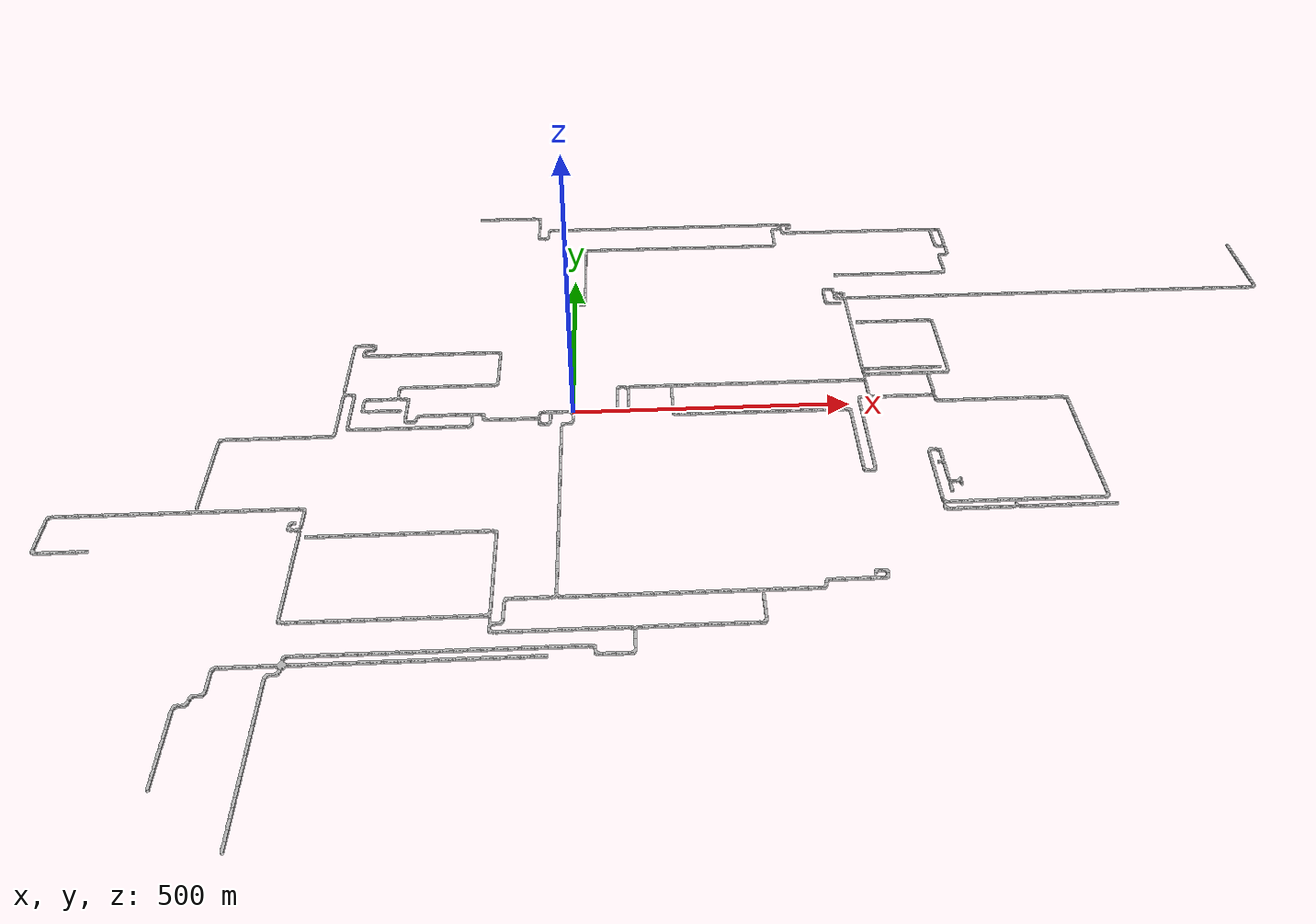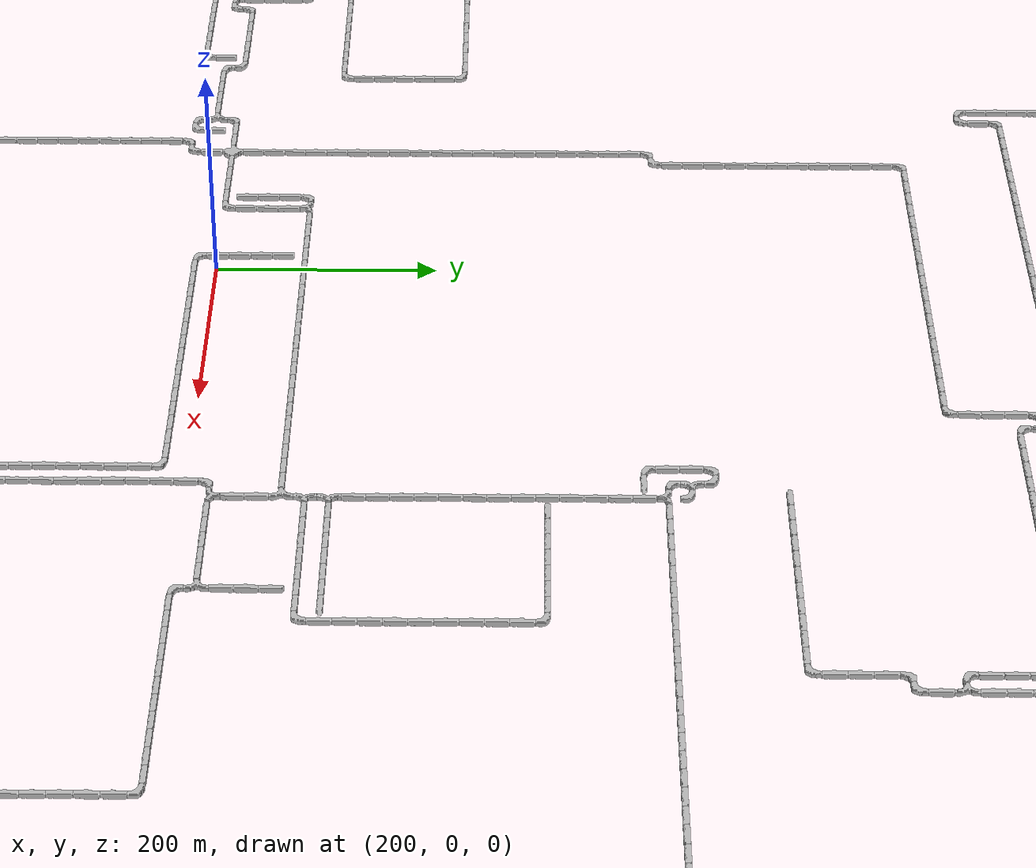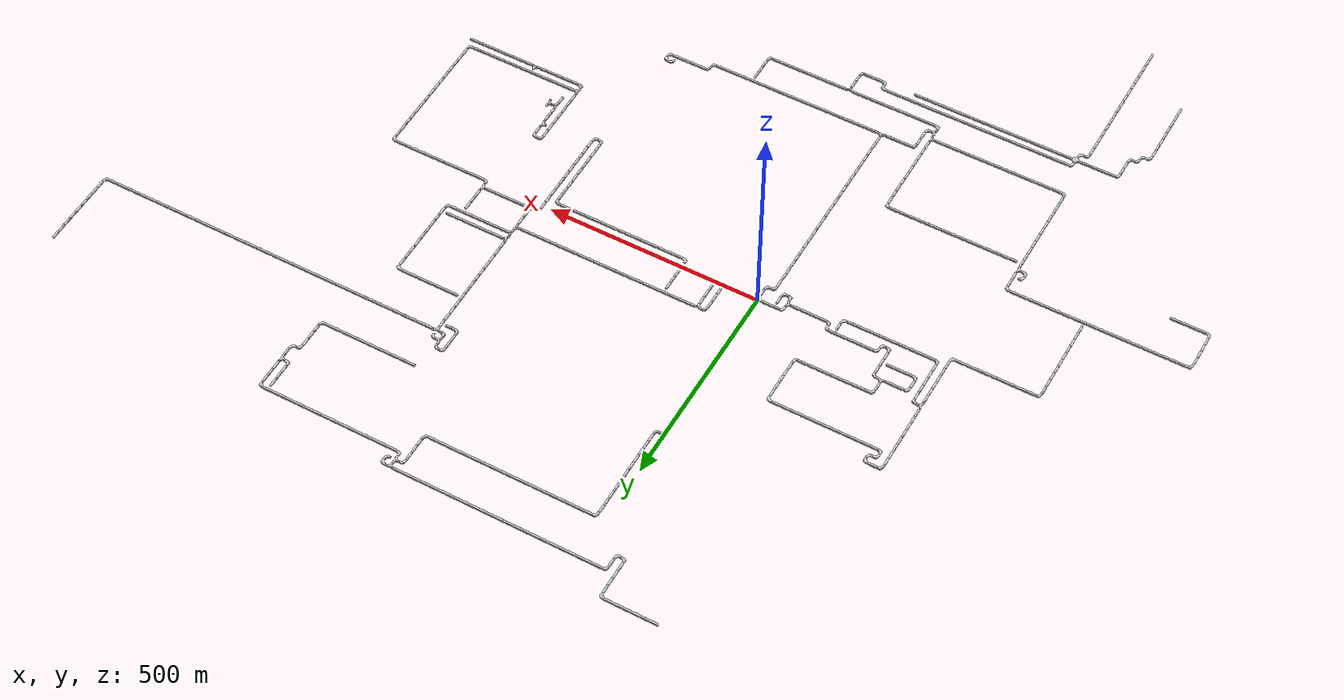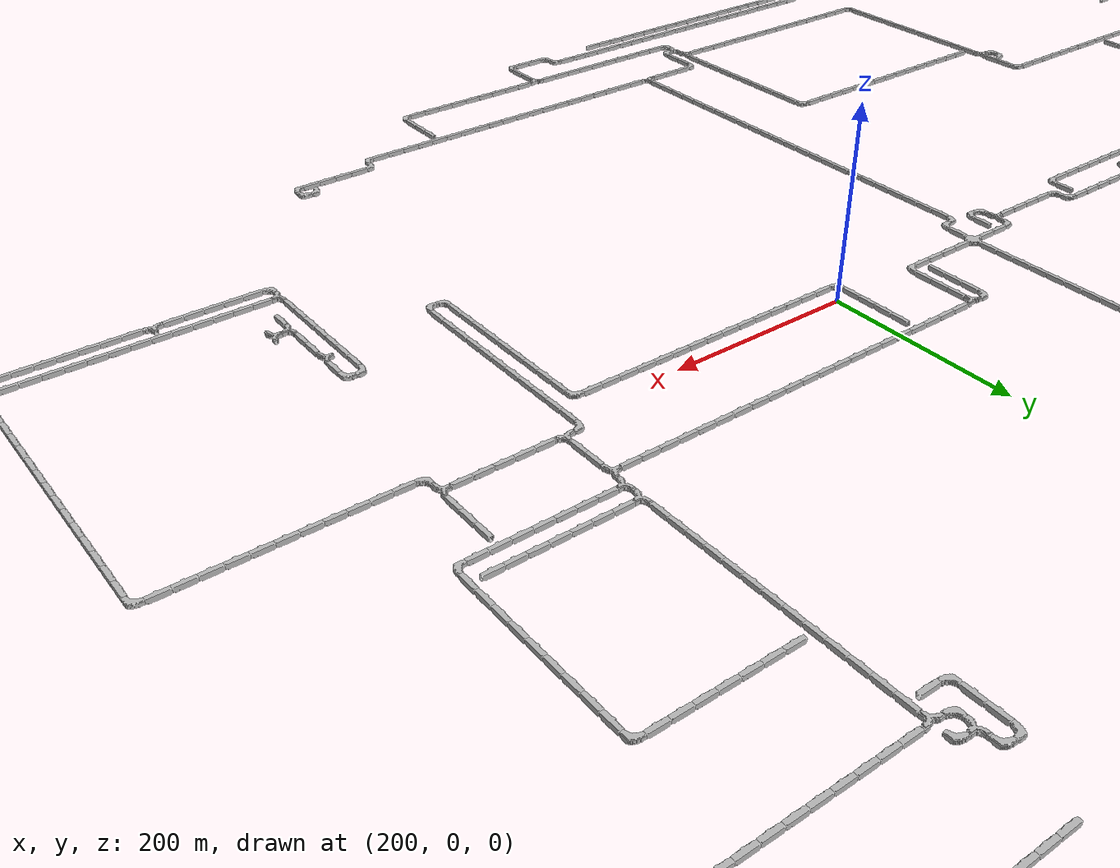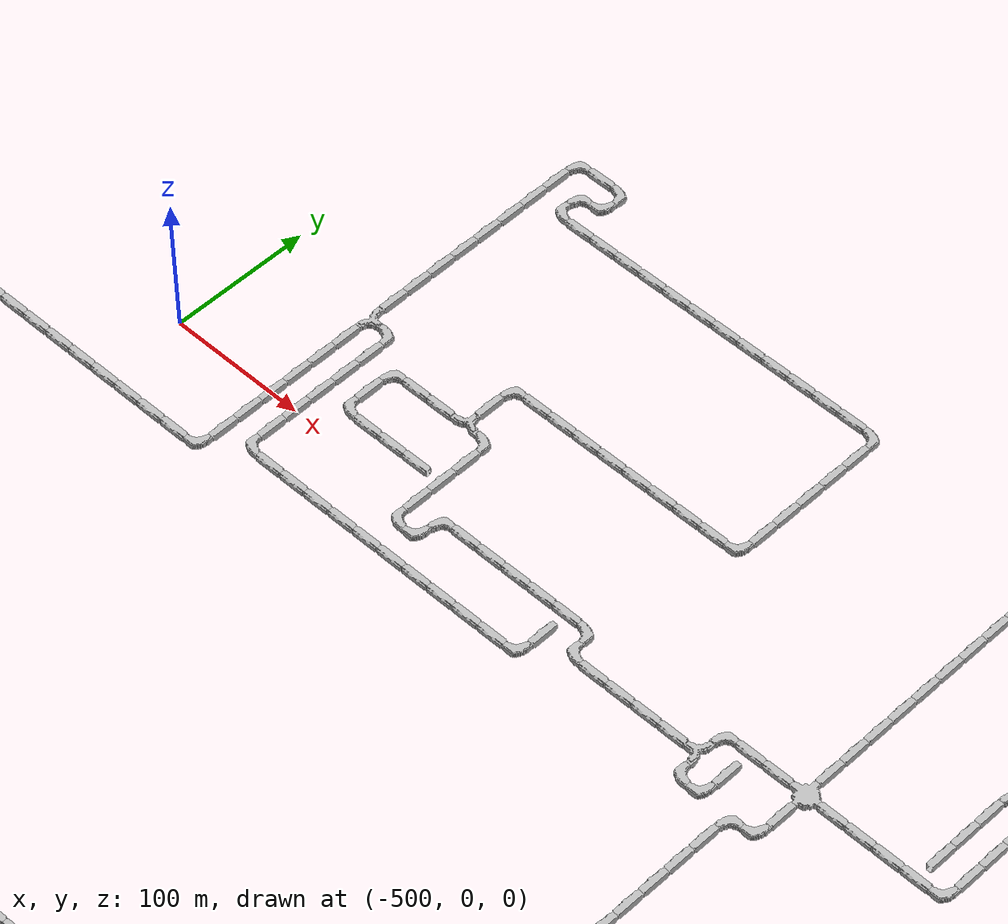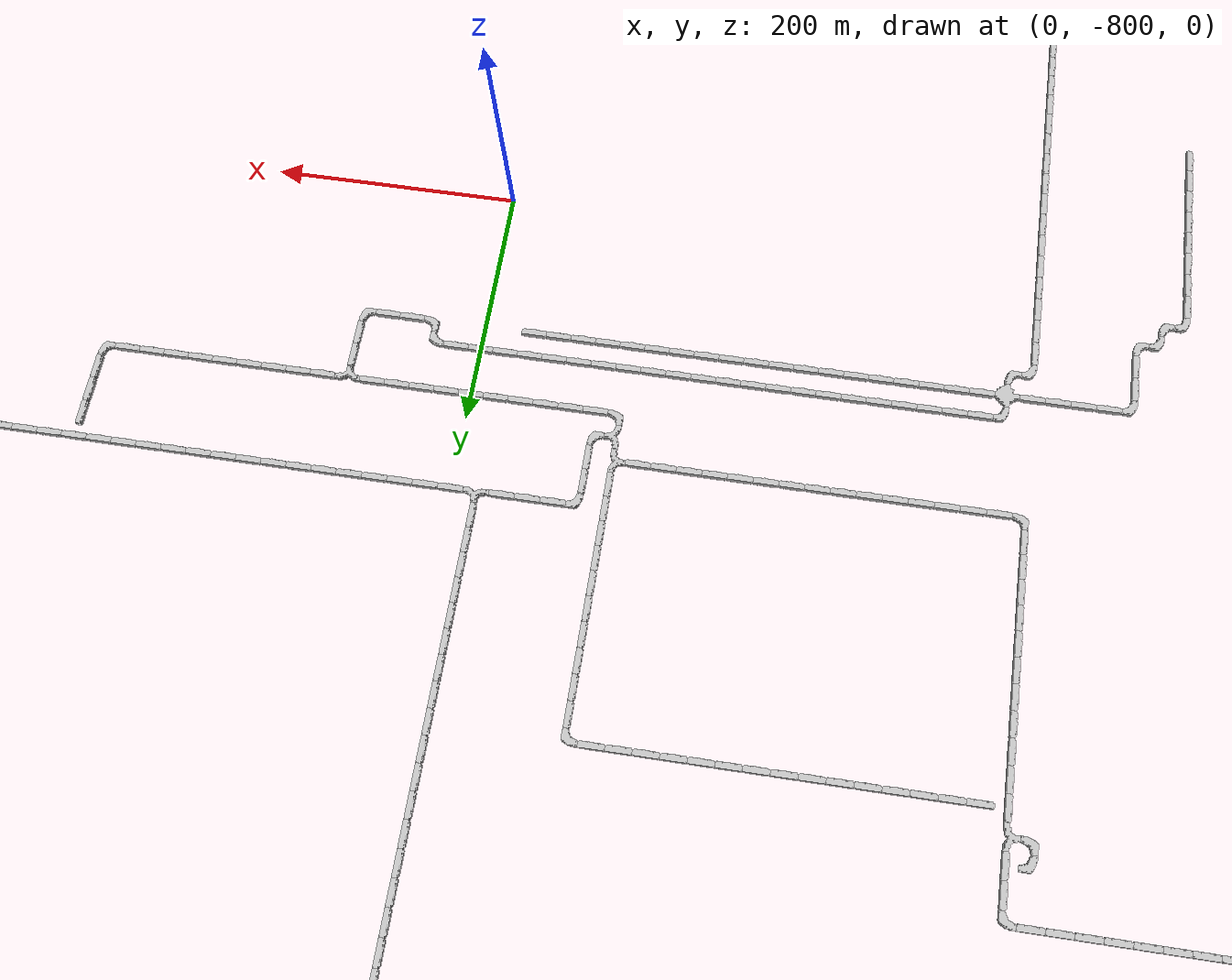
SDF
<sdf version="1.6">
 <world name="cave_16000_4">
  <include>
   <static>true</static>
   <name>cave_0_0</name>
   <pose>0 0 0 0 0 -1.5707963267948966</pose>
   <uri>model://cave_4way_20m</uri>
  </include>
  <include>
   <static>true</static>
   <name>cave_1_0</name>
   <pose>20 0 0 0 0 1.5707963267948966</pose>
   <uri>model://cave_straight_20m</uri>
  </include>
  <include>
   <static>true</static>
   <name>cave_2_0</name>
   <pose>40 0 0 0 0 1.5707963267948966</pose>
   <uri>model://cave_straight_20m</uri>
  </include>
  <include>
   <static>true</static>
   <name>cave_3_0</name>
   <pose>60 0 0 0 0 1.5707963267948966</pose>
   <uri>model://cave_straight_20m</uri>
  </include>
  <include>
   <static>true</static>
   <name>cave_4_0</name>
   <pose>80 0 0 0 0 1.5707963267948966</pose>
   <uri>model://cave_straight_20m</uri>
  </include>
  <include>
   <static>true</static>
   <name>cave_5_0</name>
   <pose>100 0 0 0 0 1.5707963267948966</pose>
   <uri>model://cave_L_20m</uri>
  </include>
  <include>
   <static>true</static>
   <name>cave_5_1</name>
   <pose>100 20 0 0 0 0.0</pose>
   <uri>model://cave_straight_20m</uri>
  </include>
  <include>
   <static>true</static>
   <name>cave_5_2</name>
   <pose>100 40 0 0 0 0.0</pose>
   <uri>model://cave_straight_20m</uri>
  </include>
  <include>
   <static>true</static>
   <name>cave_5_3</name>
   <pose>100 60 0 0 0 0.0</pose>
   <uri>model://cave_straight_20m</uri>
  </include>
  <include>
   <static>true</static>
   <name>cave_5_4</name>
   <pose>100 80 0 0 0 3.141592653589793</pose>
   <uri>model://cave_3way_20m</uri>
  </include>
  <include>
   <static>true</static>
   <name>cave_6_4</name>
   <pose>120 80 0 0 0 1.5707963267948966</pose>
   <uri>model://cave_straight_20m</uri>
  </include>
  <include>
   <static>true</static>
   <name>cave_7_4</name>
   <pose>140 80 0 0 0 1.5707963267948966</pose>
   <uri>model://cave_straight_20m</uri>
  </include>
  <include>
   <static>true</static>
   <name>cave_8_4</name>
   <pose>160 80 0 0 0 1.5707963267948966</pose>
   <uri>model://cave_straight_20m</uri>
  </include>
  <include>
   <static>true</static>
   <name>cave_9_4</name>
   <pose>180 80 0 0 0 1.5707963267948966</pose>
   <uri>model://cave_straight_20m</uri>
  </include>
  <include>
   <static>true</static>
   <name>cave_10_4</name>
   <pose>200 80 0 0 0 1.5707963267948966</pose>
   <uri>model://cave_straight_20m</uri>
  </include>
  <include>
   <static>true</static>
   <name>cave_11_4</name>
   <pose>220 80 0 0 0 1.5707963267948966</pose>
   <uri>model://cave_straight_20m</uri>
  </include>
  <include>
   <static>true</static>
   <name>cave_12_4</name>
   <pose>240 80 0 0 0 1.5707963267948966</pose>
   <uri>model://cave_straight_20m</uri>
  </include>
  <include>
   <static>true</static>
   <name>cave_13_4</name>
   <pose>260 80 0 0 0 1.5707963267948966</pose>
   <uri>model://cave_straight_20m</uri>
  </include>
  <include>
   <static>true</static>
   <name>cave_14_4</name>
   <pose>280 80 0 0 0 1.5707963267948966</pose>
   <uri>model://cave_straight_20m</uri>
  </include>
  <include>
   <static>true</static>
   <name>cave_15_4</name>
   <pose>300 80 0 0 0 1.5707963267948966</pose>
   <uri>model://cave_straight_20m</uri>
  </include>
  <include>
   <static>true</static>
   <name>cave_16_4</name>
   <pose>320 80 0 0 0 1.5707963267948966</pose>
   <uri>model://cave_straight_20m</uri>
  </include>
  <include>
   <static>true</static>
   <name>cave_17_4</name>
   <pose>340 80 0 0 0 1.5707963267948966</pose>
   <uri>model://cave_straight_20m</uri>
  </include>
  <include>
   <static>true</static>
   <name>cave_18_4</name>
   <pose>360 80 0 0 0 1.5707963267948966</pose>
   <uri>model://cave_straight_20m</uri>
  </include>
  <include>
   <static>true</static>
   <name>cave_19_4</name>
   <pose>380 80 0 0 0 1.5707963267948966</pose>
   <uri>model://cave_straight_20m</uri>
  </include>
  <include>
   <static>true</static>
   <name>cave_20_4</name>
   <pose>400 80 0 0 0 1.5707963267948966</pose>
   <uri>model://cave_straight_20m</uri>
  </include>
  <include>
   <static>true</static>
   <name>cave_21_4</name>
   <pose>420 80 0 0 0 1.5707963267948966</pose>
   <uri>model://cave_straight_20m</uri>
  </include>
  <include>
   <static>true</static>
   <name>cave_22_4</name>
   <pose>440 80 0 0 0 1.5707963267948966</pose>
   <uri>model://cave_straight_20m</uri>
  </include>
  <include>
   <static>true</static>
   <name>cave_23_4</name>
   <pose>460 80 0 0 0 1.5707963267948966</pose>
   <uri>model://cave_straight_20m</uri>
  </include>
  <include>
   <static>true</static>
   <name>cave_24_4</name>
   <pose>480 80 0 0 0 1.5707963267948966</pose>
   <uri>model://cave_straight_20m</uri>
  </include>
  <include>
   <static>true</static>
   <name>cave_25_4</name>
   <pose>500 80 0 0 0 1.5707963267948966</pose>
   <uri>model://cave_straight_20m</uri>
  </include>
  <include>
   <static>true</static>
   <name>cave_26_4</name>
   <pose>520 80 0 0 0 1.5707963267948966</pose>
   <uri>model://cave_straight_20m</uri>
  </include>
  <include>
   <static>true</static>
   <name>cave_27_4</name>
   <pose>540 80 0 0 0 1.5707963267948966</pose>
   <uri>model://cave_3way_20m</uri>
  </include>
  <include>
   <static>true</static>
   <name>cave_27_3</name>
   <pose>540 60 0 0 0 0.0</pose>
   <uri>model://cave_straight_20m</uri>
  </include>
  <include>
   <static>true</static>
   <name>cave_27_2</name>
   <pose>540 40 0 0 0 0.0</pose>
   <uri>model://cave_straight_20m</uri>
  </include>
  <include>
   <static>true</static>
   <name>cave_27_1</name>
   <pose>540 20 0 0 0 0.0</pose>
   <uri>model://cave_3way_20m</uri>
  </include>
  <include>
   <static>true</static>
   <name>cave_28_1</name>
   <pose>560 20 0 0 0 1.5707963267948966</pose>
   <uri>model://cave_straight_20m</uri>
  </include>
  <include>
   <static>true</static>
   <name>cave_29_1</name>
   <pose>580 20 0 0 0 1.5707963267948966</pose>
   <uri>model://cave_straight_20m</uri>
  </include>
  <include>
   <static>true</static>
   <name>cave_30_1</name>
   <pose>600 20 0 0 0 1.5707963267948966</pose>
   <uri>model://cave_straight_20m</uri>
  </include>
  <include>
   <static>true</static>
   <name>cave_31_1</name>
   <pose>620 20 0 0 0 1.5707963267948966</pose>
   <uri>model://cave_straight_20m</uri>
  </include>
  <include>
   <static>true</static>
   <name>cave_32_1</name>
   <pose>640 20 0 0 0 1.5707963267948966</pose>
   <uri>model://cave_straight_20m</uri>
  </include>
  <include>
   <static>true</static>
   <name>cave_33_1</name>
   <pose>660 20 0 0 0 1.5707963267948966</pose>
   <uri>model://cave_3way_20m</uri>
  </include>
  <include>
   <static>true</static>
   <name>cave_33_0</name>
   <pose>660 0 0 0 0 0.0</pose>
   <uri>model://cave_L_20m</uri>
  </include>
  <include>
   <static>true</static>
   <name>cave_34_0</name>
   <pose>680 0 0 0 0 1.5707963267948966</pose>
   <uri>model://cave_straight_20m</uri>
  </include>
  <include>
   <static>true</static>
   <name>cave_35_0</name>
   <pose>700 0 0 0 0 1.5707963267948966</pose>
   <uri>model://cave_straight_20m</uri>
  </include>
  <include>
   <static>true</static>
   <name>cave_36_0</name>
   <pose>720 0 0 0 0 1.5707963267948966</pose>
   <uri>model://cave_straight_20m</uri>
  </include>
  <include>
   <static>true</static>
   <name>cave_37_0</name>
   <pose>740 0 0 0 0 1.5707963267948966</pose>
   <uri>model://cave_straight_20m</uri>
  </include>
  <include>
   <static>true</static>
   <name>cave_38_0</name>
   <pose>760 0 0 0 0 1.5707963267948966</pose>
   <uri>model://cave_straight_20m</uri>
  </include>
  <include>
   <static>true</static>
   <name>cave_39_0</name>
   <pose>780 0 0 0 0 1.5707963267948966</pose>
   <uri>model://cave_straight_20m</uri>
  </include>
  <include>
   <static>true</static>
   <name>cave_40_0</name>
   <pose>800 0 0 0 0 1.5707963267948966</pose>
   <uri>model://cave_straight_20m</uri>
  </include>
  <include>
   <static>true</static>
   <name>cave_41_0</name>
   <pose>820 0 0 0 0 1.5707963267948966</pose>
   <uri>model://cave_straight_20m</uri>
  </include>
  <include>
   <static>true</static>
   <name>cave_42_0</name>
   <pose>840 0 0 0 0 1.5707963267948966</pose>
   <uri>model://cave_straight_20m</uri>
  </include>
  <include>
   <static>true</static>
   <name>cave_43_0</name>
   <pose>860 0 0 0 0 1.5707963267948966</pose>
   <uri>model://cave_straight_20m</uri>
  </include>
  <include>
   <static>true</static>
   <name>cave_44_0</name>
   <pose>880 0 0 0 0 1.5707963267948966</pose>
   <uri>model://cave_straight_20m</uri>
  </include>
  <include>
   <static>true</static>
   <name>cave_45_0</name>
   <pose>900 0 0 0 0 3.141592653589793</pose>
   <uri>model://cave_L_20m</uri>
  </include>
  <include>
   <static>true</static>
   <name>cave_45_-1</name>
   <pose>900 -20 0 0 0 0.0</pose>
   <uri>model://cave_straight_20m</uri>
  </include>
  <include>
   <static>true</static>
   <name>cave_45_-2</name>
   <pose>900 -40 0 0 0 0.0</pose>
   <uri>model://cave_straight_20m</uri>
  </include>
  <include>
   <static>true</static>
   <name>cave_45_-3</name>
   <pose>900 -60 0 0 0 0.0</pose>
   <uri>model://cave_straight_20m</uri>
  </include>
  <include>
   <static>true</static>
   <name>cave_45_-4</name>
   <pose>900 -80 0 0 0 0.0</pose>
   <uri>model://cave_straight_20m</uri>
  </include>
  <include>
   <static>true</static>
   <name>cave_45_-5</name>
   <pose>900 -100 0 0 0 0.0</pose>
   <uri>model://cave_straight_20m</uri>
  </include>
  <include>
   <static>true</static>
   <name>cave_45_-6</name>
   <pose>900 -120 0 0 0 0.0</pose>
   <uri>model://cave_straight_20m</uri>
  </include>
  <include>
   <static>true</static>
   <name>cave_45_-7</name>
   <pose>900 -140 0 0 0 0.0</pose>
   <uri>model://cave_straight_20m</uri>
  </include>
  <include>
   <static>true</static>
   <name>cave_45_-8</name>
   <pose>900 -160 0 0 0 0.0</pose>
   <uri>model://cave_straight_20m</uri>
  </include>
  <include>
   <static>true</static>
   <name>cave_45_-9</name>
   <pose>900 -180 0 0 0 0.0</pose>
   <uri>model://cave_straight_20m</uri>
  </include>
  <include>
   <static>true</static>
   <name>cave_45_-10</name>
   <pose>900 -200 0 0 0 0.0</pose>
   <uri>model://cave_straight_20m</uri>
  </include>
  <include>
   <static>true</static>
   <name>cave_45_-11</name>
   <pose>900 -220 0 0 0 0.0</pose>
   <uri>model://cave_straight_20m</uri>
  </include>
  <include>
   <static>true</static>
   <name>cave_45_-12</name>
   <pose>900 -240 0 0 0 0.0</pose>
   <uri>model://cave_straight_20m</uri>
  </include>
  <include>
   <static>true</static>
   <name>cave_45_-13</name>
   <pose>900 -260 0 0 0 0.0</pose>
   <uri>model://cave_straight_20m</uri>
  </include>
  <include>
   <static>true</static>
   <name>cave_45_-14</name>
   <pose>900 -280 0 0 0 0.0</pose>
   <uri>model://cave_straight_20m</uri>
  </include>
  <include>
   <static>true</static>
   <name>cave_45_-15</name>
   <pose>900 -300 0 0 0 0.0</pose>
   <uri>model://cave_straight_20m</uri>
  </include>
  <include>
   <static>true</static>
   <name>cave_45_-16</name>
   <pose>900 -320 0 0 0 1.5707963267948966</pose>
   <uri>model://cave_L_20m</uri>
  </include>
  <include>
   <static>true</static>
   <name>cave_44_-16</name>
   <pose>880 -320 0 0 0 1.5707963267948966</pose>
   <uri>model://cave_straight_20m</uri>
  </include>
  <include>
   <static>true</static>
   <name>cave_43_-16</name>
   <pose>860 -320 0 0 0 1.5707963267948966</pose>
   <uri>model://cave_straight_20m</uri>
  </include>
  <include>
   <static>true</static>
   <name>cave_42_-16</name>
   <pose>840 -320 0 0 0 1.5707963267948966</pose>
   <uri>model://cave_straight_20m</uri>
  </include>
  <include>
   <static>true</static>
   <name>cave_41_-16</name>
   <pose>820 -320 0 0 0 1.5707963267948966</pose>
   <uri>model://cave_straight_20m</uri>
  </include>
  <include>
   <static>true</static>
   <name>cave_40_-16</name>
   <pose>800 -320 0 0 0 1.5707963267948966</pose>
   <uri>model://cave_straight_20m</uri>
  </include>
  <include>
   <static>true</static>
   <name>cave_39_-16</name>
   <pose>780 -320 0 0 0 1.5707963267948966</pose>
   <uri>model://cave_straight_20m</uri>
  </include>
  <include>
   <static>true</static>
   <name>cave_38_-16</name>
   <pose>760 -320 0 0 0 1.5707963267948966</pose>
   <uri>model://cave_straight_20m</uri>
  </include>
  <include>
   <static>true</static>
   <name>cave_37_-16</name>
   <pose>740 -320 0 0 0 1.5707963267948966</pose>
   <uri>model://cave_straight_20m</uri>
  </include>
  <include>
   <static>true</static>
   <name>cave_36_-16</name>
   <pose>720 -320 0 0 0 1.5707963267948966</pose>
   <uri>model://cave_straight_20m</uri>
  </include>
  <include>
   <static>true</static>
   <name>cave_35_-16</name>
   <pose>700 -320 0 0 0 1.5707963267948966</pose>
   <uri>model://cave_straight_20m</uri>
  </include>
  <include>
   <static>true</static>
   <name>cave_34_-16</name>
   <pose>680 -320 0 0 0 1.5707963267948966</pose>
   <uri>model://cave_straight_20m</uri>
  </include>
  <include>
   <static>true</static>
   <name>cave_33_-16</name>
   <pose>660 -320 0 0 0 1.5707963267948966</pose>
   <uri>model://cave_straight_20m</uri>
  </include>
  <include>
   <static>true</static>
   <name>cave_32_-16</name>
   <pose>640 -320 0 0 0 1.5707963267948966</pose>
   <uri>model://cave_straight_20m</uri>
  </include>
  <include>
   <static>true</static>
   <name>cave_31_-16</name>
   <pose>620 -320 0 0 0 -1.5707963267948966</pose>
   <uri>model://cave_3way_20m</uri>
  </include>
  <include>
   <static>true</static>
   <name>cave_31_-17</name>
   <pose>620 -340 0 0 0 0.0</pose>
   <uri>model://cave_L_20m</uri>
  </include>
  <include>
   <static>true</static>
   <name>cave_32_-17</name>
   <pose>640 -340 0 0 0 1.5707963267948966</pose>
   <uri>model://cave_straight_20m</uri>
  </include>
  <include>
   <static>true</static>
   <name>cave_33_-17</name>
   <pose>660 -340 0 0 0 1.5707963267948966</pose>
   <uri>model://cave_straight_20m</uri>
  </include>
  <include>
   <static>true</static>
   <name>cave_34_-17</name>
   <pose>680 -340 0 0 0 1.5707963267948966</pose>
   <uri>model://cave_straight_20m</uri>
  </include>
  <include>
   <static>true</static>
   <name>cave_35_-17</name>
   <pose>700 -340 0 0 0 1.5707963267948966</pose>
   <uri>model://cave_straight_20m</uri>
  </include>
  <include>
   <static>true</static>
   <name>cave_36_-17</name>
   <pose>720 -340 0 0 0 1.5707963267948966</pose>
   <uri>model://cave_straight_20m</uri>
  </include>
  <include>
   <static>true</static>
   <name>cave_37_-17</name>
   <pose>740 -340 0 0 0 0.0</pose>
   <uri>model://cave_3way_20m</uri>
  </include>
  <include>
   <static>true</static>
   <name>cave_38_-17</name>
   <pose>760 -340 0 0 0 1.5707963267948966</pose>
   <uri>model://cave_straight_20m</uri>
  </include>
  <include>
   <static>true</static>
   <name>cave_39_-17</name>
   <pose>780 -340 0 0 0 1.5707963267948966</pose>
   <uri>model://cave_straight_20m</uri>
  </include>
  <include>
   <static>true</static>
   <name>cave_40_-17</name>
   <pose>800 -340 0 0 0 1.5707963267948966</pose>
   <uri>model://cave_straight_20m</uri>
  </include>
  <include>
   <static>true</static>
   <name>cave_41_-17</name>
   <pose>820 -340 0 0 0 1.5707963267948966</pose>
   <uri>model://cave_straight_20m</uri>
  </include>
  <include>
   <static>true</static>
   <name>cave_42_-17</name>
   <pose>840 -340 0 0 0 1.5707963267948966</pose>
   <uri>model://cave_straight_20m</uri>
  </include>
  <include>
   <static>true</static>
   <name>cave_43_-17</name>
   <pose>860 -340 0 0 0 1.5707963267948966</pose>
   <uri>model://cave_straight_20m</uri>
  </include>
  <include>
   <static>true</static>
   <name>cave_44_-17</name>
   <pose>880 -340 0 0 0 1.5707963267948966</pose>
   <uri>model://cave_straight_20m</uri>
  </include>
  <include>
   <static>true</static>
   <name>cave_45_-17</name>
   <pose>900 -340 0 0 0 1.5707963267948966</pose>
   <uri>model://cave_straight_20m</uri>
  </include>
  <include>
   <static>true</static>
   <name>cave_31_-15</name>
   <pose>620 -300 0 0 0 0.0</pose>
   <uri>model://cave_straight_20m</uri>
  </include>
  <include>
   <static>true</static>
   <name>cave_31_-14</name>
   <pose>620 -280 0 0 0 0.0</pose>
   <uri>model://cave_straight_20m</uri>
  </include>
  <include>
   <static>true</static>
   <name>cave_31_-13</name>
   <pose>620 -260 0 0 0 0.0</pose>
   <uri>model://cave_straight_20m</uri>
  </include>
  <include>
   <static>true</static>
   <name>cave_31_-12</name>
   <pose>620 -240 0 0 0 0.0</pose>
   <uri>model://cave_straight_20m</uri>
  </include>
  <include>
   <static>true</static>
   <name>cave_31_-11</name>
   <pose>620 -220 0 0 0 0.0</pose>
   <uri>model://cave_straight_20m</uri>
  </include>
  <include>
   <static>true</static>
   <name>cave_31_-10</name>
   <pose>620 -200 0 0 0 0.0</pose>
   <uri>model://cave_straight_20m</uri>
  </include>
  <include>
   <static>true</static>
   <name>cave_31_-9</name>
   <pose>620 -180 0 0 0 0.0</pose>
   <uri>model://cave_straight_20m</uri>
  </include>
  <include>
   <static>true</static>
   <name>cave_31_-8</name>
   <pose>620 -160 0 0 0 -1.5707963267948966</pose>
   <uri>model://cave_L_20m</uri>
  </include>
  <include>
   <static>true</static>
   <name>cave_32_-8</name>
   <pose>640 -160 0 0 0 3.141592653589793</pose>
   <uri>model://cave_L_20m</uri>
  </include>
  <include>
   <static>true</static>
   <name>cave_32_-9</name>
   <pose>640 -180 0 0 0 0.0</pose>
   <uri>model://cave_straight_20m</uri>
  </include>
  <include>
   <static>true</static>
   <name>cave_32_-10</name>
   <pose>640 -200 0 0 0 1.5707963267948966</pose>
   <uri>model://cave_3way_20m</uri>
  </include>
  <include>
   <static>true</static>
   <name>cave_32_-11</name>
   <pose>640 -220 0 0 0 0.0</pose>
   <uri>model://cave_straight_20m</uri>
  </include>
  <include>
   <static>true</static>
   <name>cave_32_-12</name>
   <pose>640 -240 0 0 0 0.0</pose>
   <uri>model://cave_straight_20m</uri>
  </include>
  <include>
   <static>true</static>
   <name>cave_32_-13</name>
   <pose>640 -260 0 0 0 -1.5707963267948966</pose>
   <uri>model://cave_3way_20m</uri>
  </include>
  <include>
   <static>true</static>
   <name>cave_33_-13</name>
   <pose>660 -260 0 0 0 1.5707963267948966</pose>
   <uri>model://cave_3way_20m</uri>
  </include>
  <include>
   <static>true</static>
   <name>cave_32_-14</name>
   <pose>640 -280 0 0 0 0.0</pose>
   <uri>model://cave_straight_20m</uri>
  </include>
  <include>
   <static>true</static>
   <name>cave_33_2</name>
   <pose>660 40 0 0 0 0.0</pose>
   <uri>model://cave_straight_20m</uri>
  </include>
  <include>
   <static>true</static>
   <name>cave_33_3</name>
   <pose>660 60 0 0 0 0.0</pose>
   <uri>model://cave_straight_20m</uri>
  </include>
  <include>
   <static>true</static>
   <name>cave_33_4</name>
   <pose>660 80 0 0 0 0.0</pose>
   <uri>model://cave_straight_20m</uri>
  </include>
  <include>
   <static>true</static>
   <name>cave_26_1</name>
   <pose>520 20 0 0 0 -1.5707963267948966</pose>
   <uri>model://cave_L_20m</uri>
  </include>
  <include>
   <static>true</static>
   <name>cave_26_0</name>
   <pose>520 0 0 0 0 0.0</pose>
   <uri>model://cave_straight_20m</uri>
  </include>
  <include>
   <static>true</static>
   <name>cave_26_-1</name>
   <pose>520 -20 0 0 0 0.0</pose>
   <uri>model://cave_straight_20m</uri>
  </include>
  <include>
   <static>true</static>
   <name>cave_26_-2</name>
   <pose>520 -40 0 0 0 0.0</pose>
   <uri>model://cave_straight_20m</uri>
  </include>
  <include>
   <static>true</static>
   <name>cave_26_-3</name>
   <pose>520 -60 0 0 0 0.0</pose>
   <uri>model://cave_straight_20m</uri>
  </include>
  <include>
   <static>true</static>
   <name>cave_26_-4</name>
   <pose>520 -80 0 0 0 0.0</pose>
   <uri>model://cave_straight_20m</uri>
  </include>
  <include>
   <static>true</static>
   <name>cave_26_-5</name>
   <pose>520 -100 0 0 0 0.0</pose>
   <uri>model://cave_straight_20m</uri>
  </include>
  <include>
   <static>true</static>
   <name>cave_26_-6</name>
   <pose>520 -120 0 0 0 0.0</pose>
   <uri>model://cave_straight_20m</uri>
  </include>
  <include>
   <static>true</static>
   <name>cave_26_-7</name>
   <pose>520 -140 0 0 0 0.0</pose>
   <uri>model://cave_straight_20m</uri>
  </include>
  <include>
   <static>true</static>
   <name>cave_26_-8</name>
   <pose>520 -160 0 0 0 0.0</pose>
   <uri>model://cave_straight_20m</uri>
  </include>
  <include>
   <static>true</static>
   <name>cave_26_-9</name>
   <pose>520 -180 0 0 0 0.0</pose>
   <uri>model://cave_straight_20m</uri>
  </include>
  <include>
   <static>true</static>
   <name>cave_26_-10</name>
   <pose>520 -200 0 0 0 0.0</pose>
   <uri>model://cave_straight_20m</uri>
  </include>
  <include>
   <static>true</static>
   <name>cave_26_-11</name>
   <pose>520 -220 0 0 0 1.5707963267948966</pose>
   <uri>model://cave_L_20m</uri>
  </include>
  <include>
   <static>true</static>
   <name>cave_25_-11</name>
   <pose>500 -220 0 0 0 0.0</pose>
   <uri>model://cave_L_20m</uri>
  </include>
  <include>
   <static>true</static>
   <name>cave_25_-10</name>
   <pose>500 -200 0 0 0 0.0</pose>
   <uri>model://cave_straight_20m</uri>
  </include>
  <include>
   <static>true</static>
   <name>cave_25_-9</name>
   <pose>500 -180 0 0 0 0.0</pose>
   <uri>model://cave_straight_20m</uri>
  </include>
  <include>
   <static>true</static>
   <name>cave_25_-8</name>
   <pose>500 -160 0 0 0 0.0</pose>
   <uri>model://cave_straight_20m</uri>
  </include>
  <include>
   <static>true</static>
   <name>cave_25_-7</name>
   <pose>500 -140 0 0 0 0.0</pose>
   <uri>model://cave_straight_20m</uri>
  </include>
  <include>
   <static>true</static>
   <name>cave_25_-6</name>
   <pose>500 -120 0 0 0 0.0</pose>
   <uri>model://cave_straight_20m</uri>
  </include>
  <include>
   <static>true</static>
   <name>cave_25_-5</name>
   <pose>500 -100 0 0 0 0.0</pose>
   <uri>model://cave_straight_20m</uri>
  </include>
  <include>
   <static>true</static>
   <name>cave_25_-4</name>
   <pose>500 -80 0 0 0 0.0</pose>
   <uri>model://cave_straight_20m</uri>
  </include>
  <include>
   <static>true</static>
   <name>cave_25_-3</name>
   <pose>500 -60 0 0 0 0.0</pose>
   <uri>model://cave_straight_20m</uri>
  </include>
  <include>
   <static>true</static>
   <name>cave_25_-2</name>
   <pose>500 -40 0 0 0 0.0</pose>
   <uri>model://cave_straight_20m</uri>
  </include>
  <include>
   <static>true</static>
   <name>cave_25_-1</name>
   <pose>500 -20 0 0 0 3.141592653589793</pose>
   <uri>model://cave_L_20m</uri>
  </include>
  <include>
   <static>true</static>
   <name>cave_24_-1</name>
   <pose>480 -20 0 0 0 1.5707963267948966</pose>
   <uri>model://cave_straight_20m</uri>
  </include>
  <include>
   <static>true</static>
   <name>cave_23_-1</name>
   <pose>460 -20 0 0 0 1.5707963267948966</pose>
   <uri>model://cave_straight_20m</uri>
  </include>
  <include>
   <static>true</static>
   <name>cave_22_-1</name>
   <pose>440 -20 0 0 0 1.5707963267948966</pose>
   <uri>model://cave_straight_20m</uri>
  </include>
  <include>
   <static>true</static>
   <name>cave_21_-1</name>
   <pose>420 -20 0 0 0 1.5707963267948966</pose>
   <uri>model://cave_straight_20m</uri>
  </include>
  <include>
   <static>true</static>
   <name>cave_20_-1</name>
   <pose>400 -20 0 0 0 1.5707963267948966</pose>
   <uri>model://cave_straight_20m</uri>
  </include>
  <include>
   <static>true</static>
   <name>cave_19_-1</name>
   <pose>380 -20 0 0 0 1.5707963267948966</pose>
   <uri>model://cave_straight_20m</uri>
  </include>
  <include>
   <static>true</static>
   <name>cave_18_-1</name>
   <pose>360 -20 0 0 0 1.5707963267948966</pose>
   <uri>model://cave_straight_20m</uri>
  </include>
  <include>
   <static>true</static>
   <name>cave_17_-1</name>
   <pose>340 -20 0 0 0 1.5707963267948966</pose>
   <uri>model://cave_straight_20m</uri>
  </include>
  <include>
   <static>true</static>
   <name>cave_16_-1</name>
   <pose>320 -20 0 0 0 1.5707963267948966</pose>
   <uri>model://cave_straight_20m</uri>
  </include>
  <include>
   <static>true</static>
   <name>cave_15_-1</name>
   <pose>300 -20 0 0 0 1.5707963267948966</pose>
   <uri>model://cave_straight_20m</uri>
  </include>
  <include>
   <static>true</static>
   <name>cave_14_-1</name>
   <pose>280 -20 0 0 0 1.5707963267948966</pose>
   <uri>model://cave_straight_20m</uri>
  </include>
  <include>
   <static>true</static>
   <name>cave_13_-1</name>
   <pose>260 -20 0 0 0 1.5707963267948966</pose>
   <uri>model://cave_straight_20m</uri>
  </include>
  <include>
   <static>true</static>
   <name>cave_12_-1</name>
   <pose>240 -20 0 0 0 1.5707963267948966</pose>
   <uri>model://cave_straight_20m</uri>
  </include>
  <include>
   <static>true</static>
   <name>cave_11_-1</name>
   <pose>220 -20 0 0 0 1.5707963267948966</pose>
   <uri>model://cave_straight_20m</uri>
  </include>
  <include>
   <static>true</static>
   <name>cave_10_-1</name>
   <pose>200 -20 0 0 0 1.5707963267948966</pose>
   <uri>model://cave_straight_20m</uri>
  </include>
  <include>
   <static>true</static>
   <name>cave_9_-1</name>
   <pose>180 -20 0 0 0 0.0</pose>
   <uri>model://cave_L_20m</uri>
  </include>
  <include>
   <static>true</static>
   <name>cave_9_0</name>
   <pose>180 0 0 0 0 0.0</pose>
   <uri>model://cave_straight_20m</uri>
  </include>
  <include>
   <static>true</static>
   <name>cave_9_1</name>
   <pose>180 20 0 0 0 0.0</pose>
   <uri>model://cave_straight_20m</uri>
  </include>
  <include>
   <static>true</static>
   <name>cave_9_2</name>
   <pose>180 40 0 0 0 0.0</pose>
   <uri>model://cave_straight_20m</uri>
  </include>
  <include>
   <static>true</static>
   <name>cave_9_3</name>
   <pose>180 60 0 0 0 0.0</pose>
   <uri>model://cave_straight_20m</uri>
  </include>
  <include>
   <static>true</static>
   <name>cave_27_5</name>
   <pose>540 100 0 0 0 -1.5707963267948966</pose>
   <uri>model://cave_3way_20m</uri>
  </include>
  <include>
   <static>true</static>
   <name>cave_28_5</name>
   <pose>560 100 0 0 0 1.5707963267948966</pose>
   <uri>model://cave_straight_20m</uri>
  </include>
  <include>
   <static>true</static>
   <name>cave_29_5</name>
   <pose>580 100 0 0 0 1.5707963267948966</pose>
   <uri>model://cave_straight_20m</uri>
  </include>
  <include>
   <static>true</static>
   <name>cave_30_5</name>
   <pose>600 100 0 0 0 1.5707963267948966</pose>
   <uri>model://cave_straight_20m</uri>
  </include>
  <include>
   <static>true</static>
   <name>cave_31_5</name>
   <pose>620 100 0 0 0 1.5707963267948966</pose>
   <uri>model://cave_straight_20m</uri>
  </include>
  <include>
   <static>true</static>
   <name>cave_32_5</name>
   <pose>640 100 0 0 0 1.5707963267948966</pose>
   <uri>model://cave_straight_20m</uri>
  </include>
  <include>
   <static>true</static>
   <name>cave_33_5</name>
   <pose>660 100 0 0 0 1.5707963267948966</pose>
   <uri>model://cave_straight_20m</uri>
  </include>
  <include>
   <static>true</static>
   <name>cave_34_5</name>
   <pose>680 100 0 0 0 1.5707963267948966</pose>
   <uri>model://cave_straight_20m</uri>
  </include>
  <include>
   <static>true</static>
   <name>cave_35_5</name>
   <pose>700 100 0 0 0 1.5707963267948966</pose>
   <uri>model://cave_L_20m</uri>
  </include>
  <include>
   <static>true</static>
   <name>cave_35_6</name>
   <pose>700 120 0 0 0 0.0</pose>
   <uri>model://cave_straight_20m</uri>
  </include>
  <include>
   <static>true</static>
   <name>cave_35_7</name>
   <pose>700 140 0 0 0 0.0</pose>
   <uri>model://cave_straight_20m</uri>
  </include>
  <include>
   <static>true</static>
   <name>cave_35_8</name>
   <pose>700 160 0 0 0 0.0</pose>
   <uri>model://cave_straight_20m</uri>
  </include>
  <include>
   <static>true</static>
   <name>cave_35_9</name>
   <pose>700 180 0 0 0 0.0</pose>
   <uri>model://cave_straight_20m</uri>
  </include>
  <include>
   <static>true</static>
   <name>cave_35_10</name>
   <pose>700 200 0 0 0 0.0</pose>
   <uri>model://cave_straight_20m</uri>
  </include>
  <include>
   <static>true</static>
   <name>cave_35_11</name>
   <pose>700 220 0 0 0 0.0</pose>
   <uri>model://cave_straight_20m</uri>
  </include>
  <include>
   <static>true</static>
   <name>cave_35_12</name>
   <pose>700 240 0 0 0 0.0</pose>
   <uri>model://cave_straight_20m</uri>
  </include>
  <include>
   <static>true</static>
   <name>cave_35_13</name>
   <pose>700 260 0 0 0 0.0</pose>
   <uri>model://cave_straight_20m</uri>
  </include>
  <include>
   <static>true</static>
   <name>cave_35_14</name>
   <pose>700 280 0 0 0 0.0</pose>
   <uri>model://cave_straight_20m</uri>
  </include>
  <include>
   <static>true</static>
   <name>cave_35_15</name>
   <pose>700 300 0 0 0 3.141592653589793</pose>
   <uri>model://cave_L_20m</uri>
  </include>
  <include>
   <static>true</static>
   <name>cave_34_15</name>
   <pose>680 300 0 0 0 1.5707963267948966</pose>
   <uri>model://cave_straight_20m</uri>
  </include>
  <include>
   <static>true</static>
   <name>cave_33_15</name>
   <pose>660 300 0 0 0 1.5707963267948966</pose>
   <uri>model://cave_straight_20m</uri>
  </include>
  <include>
   <static>true</static>
   <name>cave_32_15</name>
   <pose>640 300 0 0 0 1.5707963267948966</pose>
   <uri>model://cave_straight_20m</uri>
  </include>
  <include>
   <static>true</static>
   <name>cave_31_15</name>
   <pose>620 300 0 0 0 1.5707963267948966</pose>
   <uri>model://cave_straight_20m</uri>
  </include>
  <include>
   <static>true</static>
   <name>cave_30_15</name>
   <pose>600 300 0 0 0 1.5707963267948966</pose>
   <uri>model://cave_straight_20m</uri>
  </include>
  <include>
   <static>true</static>
   <name>cave_29_15</name>
   <pose>580 300 0 0 0 1.5707963267948966</pose>
   <uri>model://cave_straight_20m</uri>
  </include>
  <include>
   <static>true</static>
   <name>cave_28_15</name>
   <pose>560 300 0 0 0 1.5707963267948966</pose>
   <uri>model://cave_straight_20m</uri>
  </include>
  <include>
   <static>true</static>
   <name>cave_27_6</name>
   <pose>540 120 0 0 0 -1.5707963267948966</pose>
   <uri>model://cave_3way_20m</uri>
  </include>
  <include>
   <static>true</static>
   <name>cave_28_6</name>
   <pose>560 120 0 0 0 1.5707963267948966</pose>
   <uri>model://cave_straight_20m</uri>
  </include>
  <include>
   <static>true</static>
   <name>cave_29_6</name>
   <pose>580 120 0 0 0 1.5707963267948966</pose>
   <uri>model://cave_straight_20m</uri>
  </include>
  <include>
   <static>true</static>
   <name>cave_30_6</name>
   <pose>600 120 0 0 0 1.5707963267948966</pose>
   <uri>model://cave_straight_20m</uri>
  </include>
  <include>
   <static>true</static>
   <name>cave_31_6</name>
   <pose>620 120 0 0 0 1.5707963267948966</pose>
   <uri>model://cave_straight_20m</uri>
  </include>
  <include>
   <static>true</static>
   <name>cave_32_6</name>
   <pose>640 120 0 0 0 1.5707963267948966</pose>
   <uri>model://cave_straight_20m</uri>
  </include>
  <include>
   <static>true</static>
   <name>cave_33_6</name>
   <pose>660 120 0 0 0 1.5707963267948966</pose>
   <uri>model://cave_straight_20m</uri>
  </include>
  <include>
   <static>true</static>
   <name>cave_34_6</name>
   <pose>680 120 0 0 0 1.5707963267948966</pose>
   <uri>model://cave_straight_20m</uri>
  </include>
  <include>
   <static>true</static>
   <name>cave_27_7</name>
   <pose>540 140 0 0 0 0.0</pose>
   <uri>model://cave_straight_20m</uri>
  </include>
  <include>
   <static>true</static>
   <name>cave_27_8</name>
   <pose>540 160 0 0 0 0.0</pose>
   <uri>model://cave_straight_20m</uri>
  </include>
  <include>
   <static>true</static>
   <name>cave_27_9</name>
   <pose>540 180 0 0 0 0.0</pose>
   <uri>model://cave_straight_20m</uri>
  </include>
  <include>
   <static>true</static>
   <name>cave_27_10</name>
   <pose>540 200 0 0 0 0.0</pose>
   <uri>model://cave_straight_20m</uri>
  </include>
  <include>
   <static>true</static>
   <name>cave_27_11</name>
   <pose>540 220 0 0 0 0.0</pose>
   <uri>model://cave_straight_20m</uri>
  </include>
  <include>
   <static>true</static>
   <name>cave_27_12</name>
   <pose>540 240 0 0 0 0.0</pose>
   <uri>model://cave_straight_20m</uri>
  </include>
  <include>
   <static>true</static>
   <name>cave_27_13</name>
   <pose>540 260 0 0 0 0.0</pose>
   <uri>model://cave_straight_20m</uri>
  </include>
  <include>
   <static>true</static>
   <name>cave_27_14</name>
   <pose>540 280 0 0 0 0.0</pose>
   <uri>model://cave_straight_20m</uri>
  </include>
  <include>
   <static>true</static>
   <name>cave_27_15</name>
   <pose>540 300 0 0 0 0.0</pose>
   <uri>model://cave_straight_20m</uri>
  </include>
  <include>
   <static>true</static>
   <name>cave_27_16</name>
   <pose>540 320 0 0 0 0.0</pose>
   <uri>model://cave_straight_20m</uri>
  </include>
  <include>
   <static>true</static>
   <name>cave_27_17</name>
   <pose>540 340 0 0 0 0.0</pose>
   <uri>model://cave_straight_20m</uri>
  </include>
  <include>
   <static>true</static>
   <name>cave_27_18</name>
   <pose>540 360 0 0 0 0.0</pose>
   <uri>model://cave_straight_20m</uri>
  </include>
  <include>
   <static>true</static>
   <name>cave_27_19</name>
   <pose>540 380 0 0 0 0.0</pose>
   <uri>model://cave_straight_20m</uri>
  </include>
  <include>
   <static>true</static>
   <name>cave_27_20</name>
   <pose>540 400 0 0 0 3.141592653589793</pose>
   <uri>model://cave_3way_20m</uri>
  </include>
  <include>
   <static>true</static>
   <name>cave_28_20</name>
   <pose>560 400 0 0 0 1.5707963267948966</pose>
   <uri>model://cave_straight_20m</uri>
  </include>
  <include>
   <static>true</static>
   <name>cave_29_20</name>
   <pose>580 400 0 0 0 1.5707963267948966</pose>
   <uri>model://cave_straight_20m</uri>
  </include>
  <include>
   <static>true</static>
   <name>cave_30_20</name>
   <pose>600 400 0 0 0 1.5707963267948966</pose>
   <uri>model://cave_straight_20m</uri>
  </include>
  <include>
   <static>true</static>
   <name>cave_31_20</name>
   <pose>620 400 0 0 0 1.5707963267948966</pose>
   <uri>model://cave_straight_20m</uri>
  </include>
  <include>
   <static>true</static>
   <name>cave_32_20</name>
   <pose>640 400 0 0 0 1.5707963267948966</pose>
   <uri>model://cave_straight_20m</uri>
  </include>
  <include>
   <static>true</static>
   <name>cave_33_20</name>
   <pose>660 400 0 0 0 1.5707963267948966</pose>
   <uri>model://cave_straight_20m</uri>
  </include>
  <include>
   <static>true</static>
   <name>cave_34_20</name>
   <pose>680 400 0 0 0 1.5707963267948966</pose>
   <uri>model://cave_straight_20m</uri>
  </include>
  <include>
   <static>true</static>
   <name>cave_35_20</name>
   <pose>700 400 0 0 0 1.5707963267948966</pose>
   <uri>model://cave_straight_20m</uri>
  </include>
  <include>
   <static>true</static>
   <name>cave_36_20</name>
   <pose>720 400 0 0 0 1.5707963267948966</pose>
   <uri>model://cave_straight_20m</uri>
  </include>
  <include>
   <static>true</static>
   <name>cave_37_20</name>
   <pose>740 400 0 0 0 1.5707963267948966</pose>
   <uri>model://cave_straight_20m</uri>
  </include>
  <include>
   <static>true</static>
   <name>cave_38_20</name>
   <pose>760 400 0 0 0 1.5707963267948966</pose>
   <uri>model://cave_straight_20m</uri>
  </include>
  <include>
   <static>true</static>
   <name>cave_39_20</name>
   <pose>780 400 0 0 0 1.5707963267948966</pose>
   <uri>model://cave_straight_20m</uri>
  </include>
  <include>
   <static>true</static>
   <name>cave_40_20</name>
   <pose>800 400 0 0 0 1.5707963267948966</pose>
   <uri>model://cave_straight_20m</uri>
  </include>
  <include>
   <static>true</static>
   <name>cave_41_20</name>
   <pose>820 400 0 0 0 1.5707963267948966</pose>
   <uri>model://cave_straight_20m</uri>
  </include>
  <include>
   <static>true</static>
   <name>cave_42_20</name>
   <pose>840 400 0 0 0 1.5707963267948966</pose>
   <uri>model://cave_straight_20m</uri>
  </include>
  <include>
   <static>true</static>
   <name>cave_43_20</name>
   <pose>860 400 0 0 0 1.5707963267948966</pose>
   <uri>model://cave_straight_20m</uri>
  </include>
  <include>
   <static>true</static>
   <name>cave_44_20</name>
   <pose>880 400 0 0 0 1.5707963267948966</pose>
   <uri>model://cave_straight_20m</uri>
  </include>
  <include>
   <static>true</static>
   <name>cave_45_20</name>
   <pose>900 400 0 0 0 1.5707963267948966</pose>
   <uri>model://cave_straight_20m</uri>
  </include>
  <include>
   <static>true</static>
   <name>cave_46_20</name>
   <pose>920 400 0 0 0 1.5707963267948966</pose>
   <uri>model://cave_straight_20m</uri>
  </include>
  <include>
   <static>true</static>
   <name>cave_47_20</name>
   <pose>940 400 0 0 0 1.5707963267948966</pose>
   <uri>model://cave_straight_20m</uri>
  </include>
  <include>
   <static>true</static>
   <name>cave_48_20</name>
   <pose>960 400 0 0 0 1.5707963267948966</pose>
   <uri>model://cave_straight_20m</uri>
  </include>
  <include>
   <static>true</static>
   <name>cave_49_20</name>
   <pose>980 400 0 0 0 1.5707963267948966</pose>
   <uri>model://cave_straight_20m</uri>
  </include>
  <include>
   <static>true</static>
   <name>cave_50_20</name>
   <pose>1000 400 0 0 0 1.5707963267948966</pose>
   <uri>model://cave_straight_20m</uri>
  </include>
  <include>
   <static>true</static>
   <name>cave_51_20</name>
   <pose>1020 400 0 0 0 1.5707963267948966</pose>
   <uri>model://cave_straight_20m</uri>
  </include>
  <include>
   <static>true</static>
   <name>cave_52_20</name>
   <pose>1040 400 0 0 0 1.5707963267948966</pose>
   <uri>model://cave_straight_20m</uri>
  </include>
  <include>
   <static>true</static>
   <name>cave_53_20</name>
   <pose>1060 400 0 0 0 1.5707963267948966</pose>
   <uri>model://cave_straight_20m</uri>
  </include>
  <include>
   <static>true</static>
   <name>cave_54_20</name>
   <pose>1080 400 0 0 0 1.5707963267948966</pose>
   <uri>model://cave_straight_20m</uri>
  </include>
  <include>
   <static>true</static>
   <name>cave_55_20</name>
   <pose>1100 400 0 0 0 1.5707963267948966</pose>
   <uri>model://cave_straight_20m</uri>
  </include>
  <include>
   <static>true</static>
   <name>cave_56_20</name>
   <pose>1120 400 0 0 0 1.5707963267948966</pose>
   <uri>model://cave_straight_20m</uri>
  </include>
  <include>
   <static>true</static>
   <name>cave_57_20</name>
   <pose>1140 400 0 0 0 1.5707963267948966</pose>
   <uri>model://cave_straight_20m</uri>
  </include>
  <include>
   <static>true</static>
   <name>cave_58_20</name>
   <pose>1160 400 0 0 0 1.5707963267948966</pose>
   <uri>model://cave_straight_20m</uri>
  </include>
  <include>
   <static>true</static>
   <name>cave_59_20</name>
   <pose>1180 400 0 0 0 1.5707963267948966</pose>
   <uri>model://cave_straight_20m</uri>
  </include>
  <include>
   <static>true</static>
   <name>cave_60_20</name>
   <pose>1200 400 0 0 0 1.5707963267948966</pose>
   <uri>model://cave_straight_20m</uri>
  </include>
  <include>
   <static>true</static>
   <name>cave_61_20</name>
   <pose>1220 400 0 0 0 1.5707963267948966</pose>
   <uri>model://cave_straight_20m</uri>
  </include>
  <include>
   <static>true</static>
   <name>cave_62_20</name>
   <pose>1240 400 0 0 0 1.5707963267948966</pose>
   <uri>model://cave_straight_20m</uri>
  </include>
  <include>
   <static>true</static>
   <name>cave_63_20</name>
   <pose>1260 400 0 0 0 1.5707963267948966</pose>
   <uri>model://cave_straight_20m</uri>
  </include>
  <include>
   <static>true</static>
   <name>cave_64_20</name>
   <pose>1280 400 0 0 0 1.5707963267948966</pose>
   <uri>model://cave_straight_20m</uri>
  </include>
  <include>
   <static>true</static>
   <name>cave_65_20</name>
   <pose>1300 400 0 0 0 1.5707963267948966</pose>
   <uri>model://cave_straight_20m</uri>
  </include>
  <include>
   <static>true</static>
   <name>cave_66_20</name>
   <pose>1320 400 0 0 0 1.5707963267948966</pose>
   <uri>model://cave_straight_20m</uri>
  </include>
  <include>
   <static>true</static>
   <name>cave_67_20</name>
   <pose>1340 400 0 0 0 1.5707963267948966</pose>
   <uri>model://cave_straight_20m</uri>
  </include>
  <include>
   <static>true</static>
   <name>cave_68_20</name>
   <pose>1360 400 0 0 0 1.5707963267948966</pose>
   <uri>model://cave_straight_20m</uri>
  </include>
  <include>
   <static>true</static>
   <name>cave_69_20</name>
   <pose>1380 400 0 0 0 1.5707963267948966</pose>
   <uri>model://cave_L_20m</uri>
  </include>
  <include>
   <static>true</static>
   <name>cave_69_21</name>
   <pose>1380 420 0 0 0 0.0</pose>
   <uri>model://cave_straight_20m</uri>
  </include>
  <include>
   <static>true</static>
   <name>cave_69_22</name>
   <pose>1380 440 0 0 0 0.0</pose>
   <uri>model://cave_straight_20m</uri>
  </include>
  <include>
   <static>true</static>
   <name>cave_69_23</name>
   <pose>1380 460 0 0 0 0.0</pose>
   <uri>model://cave_straight_20m</uri>
  </include>
  <include>
   <static>true</static>
   <name>cave_69_24</name>
   <pose>1380 480 0 0 0 0.0</pose>
   <uri>model://cave_straight_20m</uri>
  </include>
  <include>
   <static>true</static>
   <name>cave_69_25</name>
   <pose>1380 500 0 0 0 0.0</pose>
   <uri>model://cave_straight_20m</uri>
  </include>
  <include>
   <static>true</static>
   <name>cave_69_26</name>
   <pose>1380 520 0 0 0 0.0</pose>
   <uri>model://cave_straight_20m</uri>
  </include>
  <include>
   <static>true</static>
   <name>cave_69_27</name>
   <pose>1380 540 0 0 0 0.0</pose>
   <uri>model://cave_straight_20m</uri>
  </include>
  <include>
   <static>true</static>
   <name>cave_69_28</name>
   <pose>1380 560 0 0 0 0.0</pose>
   <uri>model://cave_straight_20m</uri>
  </include>
  <include>
   <static>true</static>
   <name>cave_69_29</name>
   <pose>1380 580 0 0 0 0.0</pose>
   <uri>model://cave_straight_20m</uri>
  </include>
  <include>
   <static>true</static>
   <name>cave_26_20</name>
   <pose>520 400 0 0 0 0.0</pose>
   <uri>model://cave_L_20m</uri>
  </include>
  <include>
   <static>true</static>
   <name>cave_26_21</name>
   <pose>520 420 0 0 0 -1.5707963267948966</pose>
   <uri>model://cave_3way_20m</uri>
  </include>
  <include>
   <static>true</static>
   <name>cave_27_21</name>
   <pose>540 420 0 0 0 3.141592653589793</pose>
   <uri>model://cave_L_20m</uri>
  </include>
  <include>
   <static>true</static>
   <name>cave_26_22</name>
   <pose>520 440 0 0 0 3.141592653589793</pose>
   <uri>model://cave_L_20m</uri>
  </include>
  <include>
   <static>true</static>
   <name>cave_25_22</name>
   <pose>500 440 0 0 0 -1.5707963267948966</pose>
   <uri>model://cave_L_20m</uri>
  </include>
  <include>
   <static>true</static>
   <name>cave_25_21</name>
   <pose>500 420 0 0 0 0.0</pose>
   <uri>model://cave_straight_20m</uri>
  </include>
  <include>
   <static>true</static>
   <name>cave_25_20</name>
   <pose>500 400 0 0 0 0.0</pose>
   <uri>model://cave_straight_20m</uri>
  </include>
  <include>
   <static>true</static>
   <name>cave_25_19</name>
   <pose>500 380 0 0 0 0.0</pose>
   <uri>model://cave_L_20m</uri>
  </include>
  <include>
   <static>true</static>
   <name>cave_26_19</name>
   <pose>520 380 0 0 0 1.5707963267948966</pose>
   <uri>model://cave_straight_20m</uri>
  </include>
  <include>
   <static>true</static>
   <name>cave_4_4</name>
   <pose>80 80 0 0 0 -1.5707963267948966</pose>
   <uri>model://cave_L_20m</uri>
  </include>
  <include>
   <static>true</static>
   <name>cave_4_3</name>
   <pose>80 60 0 0 0 0.0</pose>
   <uri>model://cave_straight_20m</uri>
  </include>
  <include>
   <static>true</static>
   <name>cave_4_2</name>
   <pose>80 40 0 0 0 0.0</pose>
   <uri>model://cave_straight_20m</uri>
  </include>
  <include>
   <static>true</static>
   <name>cave_4_1</name>
   <pose>80 20 0 0 0 0.0</pose>
   <uri>model://cave_straight_20m</uri>
  </include>
  <include>
   <static>true</static>
   <name>cave_0_-1</name>
   <pose>0 -20 0 0 0 0.0</pose>
   <uri>model://cave_straight_20m</uri>
  </include>
  <include>
   <static>true</static>
   <name>cave_0_-2</name>
   <pose>0 -40 0 0 0 1.5707963267948966</pose>
   <uri>model://cave_L_20m</uri>
  </include>
  <include>
   <static>true</static>
   <name>cave_-1_-2</name>
   <pose>-20 -40 0 0 0 -1.5707963267948966</pose>
   <uri>model://cave_L_20m</uri>
  </include>
  <include>
   <static>true</static>
   <name>cave_-1_-3</name>
   <pose>-20 -60 0 0 0 0.0</pose>
   <uri>model://cave_straight_20m</uri>
  </include>
  <include>
   <static>true</static>
   <name>cave_-1_-4</name>
   <pose>-20 -80 0 0 0 0.0</pose>
   <uri>model://cave_straight_20m</uri>
  </include>
  <include>
   <static>true</static>
   <name>cave_-1_-5</name>
   <pose>-20 -100 0 0 0 0.0</pose>
   <uri>model://cave_straight_20m</uri>
  </include>
  <include>
   <static>true</static>
   <name>cave_-1_-6</name>
   <pose>-20 -120 0 0 0 0.0</pose>
   <uri>model://cave_straight_20m</uri>
  </include>
  <include>
   <static>true</static>
   <name>cave_-1_-7</name>
   <pose>-20 -140 0 0 0 0.0</pose>
   <uri>model://cave_straight_20m</uri>
  </include>
  <include>
   <static>true</static>
   <name>cave_-1_-8</name>
   <pose>-20 -160 0 0 0 0.0</pose>
   <uri>model://cave_straight_20m</uri>
  </include>
  <include>
   <static>true</static>
   <name>cave_-1_-9</name>
   <pose>-20 -180 0 0 0 0.0</pose>
   <uri>model://cave_straight_20m</uri>
  </include>
  <include>
   <static>true</static>
   <name>cave_-1_-10</name>
   <pose>-20 -200 0 0 0 0.0</pose>
   <uri>model://cave_straight_20m</uri>
  </include>
  <include>
   <static>true</static>
   <name>cave_-1_-11</name>
   <pose>-20 -220 0 0 0 0.0</pose>
   <uri>model://cave_straight_20m</uri>
  </include>
  <include>
   <static>true</static>
   <name>cave_-1_-12</name>
   <pose>-20 -240 0 0 0 0.0</pose>
   <uri>model://cave_straight_20m</uri>
  </include>
  <include>
   <static>true</static>
   <name>cave_-1_-13</name>
   <pose>-20 -260 0 0 0 0.0</pose>
   <uri>model://cave_straight_20m</uri>
  </include>
  <include>
   <static>true</static>
   <name>cave_-1_-14</name>
   <pose>-20 -280 0 0 0 0.0</pose>
   <uri>model://cave_straight_20m</uri>
  </include>
  <include>
   <static>true</static>
   <name>cave_-1_-15</name>
   <pose>-20 -300 0 0 0 0.0</pose>
   <uri>model://cave_straight_20m</uri>
  </include>
  <include>
   <static>true</static>
   <name>cave_-1_-16</name>
   <pose>-20 -320 0 0 0 0.0</pose>
   <uri>model://cave_straight_20m</uri>
  </include>
  <include>
   <static>true</static>
   <name>cave_-1_-17</name>
   <pose>-20 -340 0 0 0 0.0</pose>
   <uri>model://cave_straight_20m</uri>
  </include>
  <include>
   <static>true</static>
   <name>cave_-1_-18</name>
   <pose>-20 -360 0 0 0 0.0</pose>
   <uri>model://cave_straight_20m</uri>
  </include>
  <include>
   <static>true</static>
   <name>cave_-1_-19</name>
   <pose>-20 -380 0 0 0 0.0</pose>
   <uri>model://cave_straight_20m</uri>
  </include>
  <include>
   <static>true</static>
   <name>cave_-1_-20</name>
   <pose>-20 -400 0 0 0 0.0</pose>
   <uri>model://cave_straight_20m</uri>
  </include>
  <include>
   <static>true</static>
   <name>cave_-1_-21</name>
   <pose>-20 -420 0 0 0 0.0</pose>
   <uri>model://cave_straight_20m</uri>
  </include>
  <include>
   <static>true</static>
   <name>cave_-1_-22</name>
   <pose>-20 -440 0 0 0 0.0</pose>
   <uri>model://cave_straight_20m</uri>
  </include>
  <include>
   <static>true</static>
   <name>cave_-1_-23</name>
   <pose>-20 -460 0 0 0 0.0</pose>
   <uri>model://cave_straight_20m</uri>
  </include>
  <include>
   <static>true</static>
   <name>cave_-1_-24</name>
   <pose>-20 -480 0 0 0 0.0</pose>
   <uri>model://cave_straight_20m</uri>
  </include>
  <include>
   <static>true</static>
   <name>cave_-1_-25</name>
   <pose>-20 -500 0 0 0 0.0</pose>
   <uri>model://cave_straight_20m</uri>
  </include>
  <include>
   <static>true</static>
   <name>cave_-1_-26</name>
   <pose>-20 -520 0 0 0 0.0</pose>
   <uri>model://cave_straight_20m</uri>
  </include>
  <include>
   <static>true</static>
   <name>cave_-1_-27</name>
   <pose>-20 -540 0 0 0 0.0</pose>
   <uri>model://cave_3way_20m</uri>
  </include>
  <include>
   <static>true</static>
   <name>cave_0_-27</name>
   <pose>0 -540 0 0 0 1.5707963267948966</pose>
   <uri>model://cave_straight_20m</uri>
  </include>
  <include>
   <static>true</static>
   <name>cave_1_-27</name>
   <pose>20 -540 0 0 0 1.5707963267948966</pose>
   <uri>model://cave_straight_20m</uri>
  </include>
  <include>
   <static>true</static>
   <name>cave_2_-27</name>
   <pose>40 -540 0 0 0 1.5707963267948966</pose>
   <uri>model://cave_straight_20m</uri>
  </include>
  <include>
   <static>true</static>
   <name>cave_3_-27</name>
   <pose>60 -540 0 0 0 1.5707963267948966</pose>
   <uri>model://cave_straight_20m</uri>
  </include>
  <include>
   <static>true</static>
   <name>cave_4_-27</name>
   <pose>80 -540 0 0 0 1.5707963267948966</pose>
   <uri>model://cave_straight_20m</uri>
  </include>
  <include>
   <static>true</static>
   <name>cave_5_-27</name>
   <pose>100 -540 0 0 0 1.5707963267948966</pose>
   <uri>model://cave_straight_20m</uri>
  </include>
  <include>
   <static>true</static>
   <name>cave_6_-27</name>
   <pose>120 -540 0 0 0 1.5707963267948966</pose>
   <uri>model://cave_straight_20m</uri>
  </include>
  <include>
   <static>true</static>
   <name>cave_7_-27</name>
   <pose>140 -540 0 0 0 1.5707963267948966</pose>
   <uri>model://cave_straight_20m</uri>
  </include>
  <include>
   <static>true</static>
   <name>cave_8_-27</name>
   <pose>160 -540 0 0 0 1.5707963267948966</pose>
   <uri>model://cave_straight_20m</uri>
  </include>
  <include>
   <static>true</static>
   <name>cave_9_-27</name>
   <pose>180 -540 0 0 0 1.5707963267948966</pose>
   <uri>model://cave_straight_20m</uri>
  </include>
  <include>
   <static>true</static>
   <name>cave_10_-27</name>
   <pose>200 -540 0 0 0 1.5707963267948966</pose>
   <uri>model://cave_straight_20m</uri>
  </include>
  <include>
   <static>true</static>
   <name>cave_11_-27</name>
   <pose>220 -540 0 0 0 1.5707963267948966</pose>
   <uri>model://cave_straight_20m</uri>
  </include>
  <include>
   <static>true</static>
   <name>cave_12_-27</name>
   <pose>240 -540 0 0 0 1.5707963267948966</pose>
   <uri>model://cave_straight_20m</uri>
  </include>
  <include>
   <static>true</static>
   <name>cave_13_-27</name>
   <pose>260 -540 0 0 0 1.5707963267948966</pose>
   <uri>model://cave_straight_20m</uri>
  </include>
  <include>
   <static>true</static>
   <name>cave_14_-27</name>
   <pose>280 -540 0 0 0 1.5707963267948966</pose>
   <uri>model://cave_straight_20m</uri>
  </include>
  <include>
   <static>true</static>
   <name>cave_15_-27</name>
   <pose>300 -540 0 0 0 1.5707963267948966</pose>
   <uri>model://cave_straight_20m</uri>
  </include>
  <include>
   <static>true</static>
   <name>cave_16_-27</name>
   <pose>320 -540 0 0 0 1.5707963267948966</pose>
   <uri>model://cave_straight_20m</uri>
  </include>
  <include>
   <static>true</static>
   <name>cave_17_-27</name>
   <pose>340 -540 0 0 0 1.5707963267948966</pose>
   <uri>model://cave_straight_20m</uri>
  </include>
  <include>
   <static>true</static>
   <name>cave_18_-27</name>
   <pose>360 -540 0 0 0 1.5707963267948966</pose>
   <uri>model://cave_straight_20m</uri>
  </include>
  <include>
   <static>true</static>
   <name>cave_19_-27</name>
   <pose>380 -540 0 0 0 1.5707963267948966</pose>
   <uri>model://cave_straight_20m</uri>
  </include>
  <include>
   <static>true</static>
   <name>cave_20_-27</name>
   <pose>400 -540 0 0 0 1.5707963267948966</pose>
   <uri>model://cave_L_20m</uri>
  </include>
  <include>
   <static>true</static>
   <name>cave_20_-26</name>
   <pose>400 -520 0 0 0 -1.5707963267948966</pose>
   <uri>model://cave_L_20m</uri>
  </include>
  <include>
   <static>true</static>
   <name>cave_21_-26</name>
   <pose>420 -520 0 0 0 1.5707963267948966</pose>
   <uri>model://cave_straight_20m</uri>
  </include>
  <include>
   <static>true</static>
   <name>cave_22_-26</name>
   <pose>440 -520 0 0 0 1.5707963267948966</pose>
   <uri>model://cave_straight_20m</uri>
  </include>
  <include>
   <static>true</static>
   <name>cave_23_-26</name>
   <pose>460 -520 0 0 0 1.5707963267948966</pose>
   <uri>model://cave_straight_20m</uri>
  </include>
  <include>
   <static>true</static>
   <name>cave_24_-26</name>
   <pose>480 -520 0 0 0 1.5707963267948966</pose>
   <uri>model://cave_straight_20m</uri>
  </include>
  <include>
   <static>true</static>
   <name>cave_25_-26</name>
   <pose>500 -520 0 0 0 1.5707963267948966</pose>
   <uri>model://cave_L_20m</uri>
  </include>
  <include>
   <static>true</static>
   <name>cave_25_-25</name>
   <pose>500 -500 0 0 0 3.141592653589793</pose>
   <uri>model://cave_L_20m</uri>
  </include>
  <include>
   <static>true</static>
   <name>cave_24_-25</name>
   <pose>480 -500 0 0 0 -1.5707963267948966</pose>
   <uri>model://cave_L_20m</uri>
  </include>
  <include>
   <static>true</static>
   <name>cave_-2_-27</name>
   <pose>-40 -540 0 0 0 1.5707963267948966</pose>
   <uri>model://cave_straight_20m</uri>
  </include>
  <include>
   <static>true</static>
   <name>cave_-3_-27</name>
   <pose>-60 -540 0 0 0 1.5707963267948966</pose>
   <uri>model://cave_straight_20m</uri>
  </include>
  <include>
   <static>true</static>
   <name>cave_-4_-27</name>
   <pose>-80 -540 0 0 0 1.5707963267948966</pose>
   <uri>model://cave_straight_20m</uri>
  </include>
  <include>
   <static>true</static>
   <name>cave_-5_-27</name>
   <pose>-100 -540 0 0 0 -1.5707963267948966</pose>
   <uri>model://cave_L_20m</uri>
  </include>
  <include>
   <static>true</static>
   <name>cave_-5_-28</name>
   <pose>-100 -560 0 0 0 0.0</pose>
   <uri>model://cave_straight_20m</uri>
  </include>
  <include>
   <static>true</static>
   <name>cave_-5_-29</name>
   <pose>-100 -580 0 0 0 0.0</pose>
   <uri>model://cave_straight_20m</uri>
  </include>
  <include>
   <static>true</static>
   <name>cave_-5_-30</name>
   <pose>-100 -600 0 0 0 1.5707963267948966</pose>
   <uri>model://cave_L_20m</uri>
  </include>
  <include>
   <static>true</static>
   <name>cave_-6_-30</name>
   <pose>-120 -600 0 0 0 -1.5707963267948966</pose>
   <uri>model://cave_3way_20m</uri>
  </include>
  <include>
   <static>true</static>
   <name>cave_-6_-31</name>
   <pose>-120 -620 0 0 0 0.0</pose>
   <uri>model://cave_L_20m</uri>
  </include>
  <include>
   <static>true</static>
   <name>cave_-5_-31</name>
   <pose>-100 -620 0 0 0 1.5707963267948966</pose>
   <uri>model://cave_straight_20m</uri>
  </include>
  <include>
   <static>true</static>
   <name>cave_-4_-31</name>
   <pose>-80 -620 0 0 0 1.5707963267948966</pose>
   <uri>model://cave_straight_20m</uri>
  </include>
  <include>
   <static>true</static>
   <name>cave_-3_-31</name>
   <pose>-60 -620 0 0 0 1.5707963267948966</pose>
   <uri>model://cave_straight_20m</uri>
  </include>
  <include>
   <static>true</static>
   <name>cave_-2_-31</name>
   <pose>-40 -620 0 0 0 1.5707963267948966</pose>
   <uri>model://cave_straight_20m</uri>
  </include>
  <include>
   <static>true</static>
   <name>cave_-1_-31</name>
   <pose>-20 -620 0 0 0 1.5707963267948966</pose>
   <uri>model://cave_straight_20m</uri>
  </include>
  <include>
   <static>true</static>
   <name>cave_0_-31</name>
   <pose>0 -620 0 0 0 1.5707963267948966</pose>
   <uri>model://cave_straight_20m</uri>
  </include>
  <include>
   <static>true</static>
   <name>cave_1_-31</name>
   <pose>20 -620 0 0 0 1.5707963267948966</pose>
   <uri>model://cave_straight_20m</uri>
  </include>
  <include>
   <static>true</static>
   <name>cave_2_-31</name>
   <pose>40 -620 0 0 0 1.5707963267948966</pose>
   <uri>model://cave_straight_20m</uri>
  </include>
  <include>
   <static>true</static>
   <name>cave_3_-31</name>
   <pose>60 -620 0 0 0 1.5707963267948966</pose>
   <uri>model://cave_straight_20m</uri>
  </include>
  <include>
   <static>true</static>
   <name>cave_4_-31</name>
   <pose>80 -620 0 0 0 1.5707963267948966</pose>
   <uri>model://cave_straight_20m</uri>
  </include>
  <include>
   <static>true</static>
   <name>cave_5_-31</name>
   <pose>100 -620 0 0 0 3.141592653589793</pose>
   <uri>model://cave_3way_20m</uri>
  </include>
  <include>
   <static>true</static>
   <name>cave_6_-31</name>
   <pose>120 -620 0 0 0 1.5707963267948966</pose>
   <uri>model://cave_straight_20m</uri>
  </include>
  <include>
   <static>true</static>
   <name>cave_7_-31</name>
   <pose>140 -620 0 0 0 1.5707963267948966</pose>
   <uri>model://cave_straight_20m</uri>
  </include>
  <include>
   <static>true</static>
   <name>cave_8_-31</name>
   <pose>160 -620 0 0 0 1.5707963267948966</pose>
   <uri>model://cave_straight_20m</uri>
  </include>
  <include>
   <static>true</static>
   <name>cave_9_-31</name>
   <pose>180 -620 0 0 0 1.5707963267948966</pose>
   <uri>model://cave_straight_20m</uri>
  </include>
  <include>
   <static>true</static>
   <name>cave_10_-31</name>
   <pose>200 -620 0 0 0 1.5707963267948966</pose>
   <uri>model://cave_straight_20m</uri>
  </include>
  <include>
   <static>true</static>
   <name>cave_11_-31</name>
   <pose>220 -620 0 0 0 1.5707963267948966</pose>
   <uri>model://cave_straight_20m</uri>
  </include>
  <include>
   <static>true</static>
   <name>cave_12_-31</name>
   <pose>240 -620 0 0 0 1.5707963267948966</pose>
   <uri>model://cave_straight_20m</uri>
  </include>
  <include>
   <static>true</static>
   <name>cave_13_-31</name>
   <pose>260 -620 0 0 0 1.5707963267948966</pose>
   <uri>model://cave_straight_20m</uri>
  </include>
  <include>
   <static>true</static>
   <name>cave_14_-31</name>
   <pose>280 -620 0 0 0 1.5707963267948966</pose>
   <uri>model://cave_straight_20m</uri>
  </include>
  <include>
   <static>true</static>
   <name>cave_15_-31</name>
   <pose>300 -620 0 0 0 1.5707963267948966</pose>
   <uri>model://cave_L_20m</uri>
  </include>
  <include>
   <static>true</static>
   <name>cave_15_-30</name>
   <pose>300 -600 0 0 0 0.0</pose>
   <uri>model://cave_straight_20m</uri>
  </include>
  <include>
   <static>true</static>
   <name>cave_15_-29</name>
   <pose>300 -580 0 0 0 0.0</pose>
   <uri>model://cave_straight_20m</uri>
  </include>
  <include>
   <static>true</static>
   <name>cave_15_-28</name>
   <pose>300 -560 0 0 0 0.0</pose>
   <uri>model://cave_straight_20m</uri>
  </include>
  <include>
   <static>true</static>
   <name>cave_5_-32</name>
   <pose>100 -640 0 0 0 0.0</pose>
   <uri>model://cave_straight_20m</uri>
  </include>
  <include>
   <static>true</static>
   <name>cave_5_-33</name>
   <pose>100 -660 0 0 0 0.0</pose>
   <uri>model://cave_straight_20m</uri>
  </include>
  <include>
   <static>true</static>
   <name>cave_5_-34</name>
   <pose>100 -680 0 0 0 1.5707963267948966</pose>
   <uri>model://cave_L_20m</uri>
  </include>
  <include>
   <static>true</static>
   <name>cave_4_-34</name>
   <pose>80 -680 0 0 0 1.5707963267948966</pose>
   <uri>model://cave_straight_20m</uri>
  </include>
  <include>
   <static>true</static>
   <name>cave_3_-34</name>
   <pose>60 -680 0 0 0 1.5707963267948966</pose>
   <uri>model://cave_straight_20m</uri>
  </include>
  <include>
   <static>true</static>
   <name>cave_2_-34</name>
   <pose>40 -680 0 0 0 0.0</pose>
   <uri>model://cave_L_20m</uri>
  </include>
  <include>
   <static>true</static>
   <name>cave_2_-33</name>
   <pose>40 -660 0 0 0 3.141592653589793</pose>
   <uri>model://cave_L_20m</uri>
  </include>
  <include>
   <static>true</static>
   <name>cave_1_-33</name>
   <pose>20 -660 0 0 0 1.5707963267948966</pose>
   <uri>model://cave_straight_20m</uri>
  </include>
  <include>
   <static>true</static>
   <name>cave_0_-33</name>
   <pose>0 -660 0 0 0 1.5707963267948966</pose>
   <uri>model://cave_straight_20m</uri>
  </include>
  <include>
   <static>true</static>
   <name>cave_-1_-33</name>
   <pose>-20 -660 0 0 0 1.5707963267948966</pose>
   <uri>model://cave_straight_20m</uri>
  </include>
  <include>
   <static>true</static>
   <name>cave_-2_-33</name>
   <pose>-40 -660 0 0 0 1.5707963267948966</pose>
   <uri>model://cave_straight_20m</uri>
  </include>
  <include>
   <static>true</static>
   <name>cave_-3_-33</name>
   <pose>-60 -660 0 0 0 1.5707963267948966</pose>
   <uri>model://cave_straight_20m</uri>
  </include>
  <include>
   <static>true</static>
   <name>cave_-4_-33</name>
   <pose>-80 -660 0 0 0 1.5707963267948966</pose>
   <uri>model://cave_straight_20m</uri>
  </include>
  <include>
   <static>true</static>
   <name>cave_-5_-33</name>
   <pose>-100 -660 0 0 0 1.5707963267948966</pose>
   <uri>model://cave_straight_20m</uri>
  </include>
  <include>
   <static>true</static>
   <name>cave_-6_-33</name>
   <pose>-120 -660 0 0 0 1.5707963267948966</pose>
   <uri>model://cave_straight_20m</uri>
  </include>
  <include>
   <static>true</static>
   <name>cave_-7_-33</name>
   <pose>-140 -660 0 0 0 1.5707963267948966</pose>
   <uri>model://cave_straight_20m</uri>
  </include>
  <include>
   <static>true</static>
   <name>cave_-8_-33</name>
   <pose>-160 -660 0 0 0 1.5707963267948966</pose>
   <uri>model://cave_straight_20m</uri>
  </include>
  <include>
   <static>true</static>
   <name>cave_-9_-33</name>
   <pose>-180 -660 0 0 0 1.5707963267948966</pose>
   <uri>model://cave_straight_20m</uri>
  </include>
  <include>
   <static>true</static>
   <name>cave_-10_-33</name>
   <pose>-200 -660 0 0 0 1.5707963267948966</pose>
   <uri>model://cave_straight_20m</uri>
  </include>
  <include>
   <static>true</static>
   <name>cave_-11_-33</name>
   <pose>-220 -660 0 0 0 1.5707963267948966</pose>
   <uri>model://cave_straight_20m</uri>
  </include>
  <include>
   <static>true</static>
   <name>cave_-12_-33</name>
   <pose>-240 -660 0 0 0 1.5707963267948966</pose>
   <uri>model://cave_straight_20m</uri>
  </include>
  <include>
   <static>true</static>
   <name>cave_-13_-33</name>
   <pose>-260 -660 0 0 0 1.5707963267948966</pose>
   <uri>model://cave_straight_20m</uri>
  </include>
  <include>
   <static>true</static>
   <name>cave_-14_-33</name>
   <pose>-280 -660 0 0 0 1.5707963267948966</pose>
   <uri>model://cave_straight_20m</uri>
  </include>
  <include>
   <static>true</static>
   <name>cave_-15_-33</name>
   <pose>-300 -660 0 0 0 1.5707963267948966</pose>
   <uri>model://cave_straight_20m</uri>
  </include>
  <include>
   <static>true</static>
   <name>cave_-16_-33</name>
   <pose>-320 -660 0 0 0 1.5707963267948966</pose>
   <uri>model://cave_straight_20m</uri>
  </include>
  <include>
   <static>true</static>
   <name>cave_-17_-33</name>
   <pose>-340 -660 0 0 0 1.5707963267948966</pose>
   <uri>model://cave_straight_20m</uri>
  </include>
  <include>
   <static>true</static>
   <name>cave_-18_-33</name>
   <pose>-360 -660 0 0 0 1.5707963267948966</pose>
   <uri>model://cave_straight_20m</uri>
  </include>
  <include>
   <static>true</static>
   <name>cave_-19_-33</name>
   <pose>-380 -660 0 0 0 1.5707963267948966</pose>
   <uri>model://cave_straight_20m</uri>
  </include>
  <include>
   <static>true</static>
   <name>cave_-20_-33</name>
   <pose>-400 -660 0 0 0 1.5707963267948966</pose>
   <uri>model://cave_straight_20m</uri>
  </include>
  <include>
   <static>true</static>
   <name>cave_-21_-33</name>
   <pose>-420 -660 0 0 0 -1.5707963267948966</pose>
   <uri>model://cave_L_20m</uri>
  </include>
  <include>
   <static>true</static>
   <name>cave_-21_-34</name>
   <pose>-420 -680 0 0 0 -1.5707963267948966</pose>
   <uri>model://cave_4way_20m</uri>
  </include>
  <include>
   <static>true</static>
   <name>cave_-20_-34</name>
   <pose>-400 -680 0 0 0 1.5707963267948966</pose>
   <uri>model://cave_straight_20m</uri>
  </include>
  <include>
   <static>true</static>
   <name>cave_-19_-34</name>
   <pose>-380 -680 0 0 0 1.5707963267948966</pose>
   <uri>model://cave_straight_20m</uri>
  </include>
  <include>
   <static>true</static>
   <name>cave_-18_-34</name>
   <pose>-360 -680 0 0 0 1.5707963267948966</pose>
   <uri>model://cave_straight_20m</uri>
  </include>
  <include>
   <static>true</static>
   <name>cave_-17_-34</name>
   <pose>-340 -680 0 0 0 1.5707963267948966</pose>
   <uri>model://cave_straight_20m</uri>
  </include>
  <include>
   <static>true</static>
   <name>cave_-16_-34</name>
   <pose>-320 -680 0 0 0 1.5707963267948966</pose>
   <uri>model://cave_straight_20m</uri>
  </include>
  <include>
   <static>true</static>
   <name>cave_-15_-34</name>
   <pose>-300 -680 0 0 0 1.5707963267948966</pose>
   <uri>model://cave_straight_20m</uri>
  </include>
  <include>
   <static>true</static>
   <name>cave_-14_-34</name>
   <pose>-280 -680 0 0 0 1.5707963267948966</pose>
   <uri>model://cave_straight_20m</uri>
  </include>
  <include>
   <static>true</static>
   <name>cave_-13_-34</name>
   <pose>-260 -680 0 0 0 1.5707963267948966</pose>
   <uri>model://cave_straight_20m</uri>
  </include>
  <include>
   <static>true</static>
   <name>cave_-12_-34</name>
   <pose>-240 -680 0 0 0 1.5707963267948966</pose>
   <uri>model://cave_straight_20m</uri>
  </include>
  <include>
   <static>true</static>
   <name>cave_-11_-34</name>
   <pose>-220 -680 0 0 0 1.5707963267948966</pose>
   <uri>model://cave_straight_20m</uri>
  </include>
  <include>
   <static>true</static>
   <name>cave_-10_-34</name>
   <pose>-200 -680 0 0 0 1.5707963267948966</pose>
   <uri>model://cave_straight_20m</uri>
  </include>
  <include>
   <static>true</static>
   <name>cave_-9_-34</name>
   <pose>-180 -680 0 0 0 1.5707963267948966</pose>
   <uri>model://cave_straight_20m</uri>
  </include>
  <include>
   <static>true</static>
   <name>cave_-8_-34</name>
   <pose>-160 -680 0 0 0 1.5707963267948966</pose>
   <uri>model://cave_straight_20m</uri>
  </include>
  <include>
   <static>true</static>
   <name>cave_-7_-34</name>
   <pose>-140 -680 0 0 0 1.5707963267948966</pose>
   <uri>model://cave_straight_20m</uri>
  </include>
  <include>
   <static>true</static>
   <name>cave_-6_-34</name>
   <pose>-120 -680 0 0 0 1.5707963267948966</pose>
   <uri>model://cave_straight_20m</uri>
  </include>
  <include>
   <static>true</static>
   <name>cave_-5_-34</name>
   <pose>-100 -680 0 0 0 1.5707963267948966</pose>
   <uri>model://cave_straight_20m</uri>
  </include>
  <include>
   <static>true</static>
   <name>cave_-4_-34</name>
   <pose>-80 -680 0 0 0 1.5707963267948966</pose>
   <uri>model://cave_straight_20m</uri>
  </include>
  <include>
   <static>true</static>
   <name>cave_-3_-34</name>
   <pose>-60 -680 0 0 0 1.5707963267948966</pose>
   <uri>model://cave_straight_20m</uri>
  </include>
  <include>
   <static>true</static>
   <name>cave_-2_-34</name>
   <pose>-40 -680 0 0 0 1.5707963267948966</pose>
   <uri>model://cave_straight_20m</uri>
  </include>
  <include>
   <static>true</static>
   <name>cave_-21_-35</name>
   <pose>-420 -700 0 0 0 1.5707963267948966</pose>
   <uri>model://cave_L_20m</uri>
  </include>
  <include>
   <static>true</static>
   <name>cave_-22_-35</name>
   <pose>-440 -700 0 0 0 -1.5707963267948966</pose>
   <uri>model://cave_L_20m</uri>
  </include>
  <include>
   <static>true</static>
   <name>cave_-22_-36</name>
   <pose>-440 -720 0 0 0 0.0</pose>
   <uri>model://cave_straight_20m</uri>
  </include>
  <include>
   <static>true</static>
   <name>cave_-22_-37</name>
   <pose>-440 -740 0 0 0 0.0</pose>
   <uri>model://cave_straight_20m</uri>
  </include>
  <include>
   <static>true</static>
   <name>cave_-22_-38</name>
   <pose>-440 -760 0 0 0 0.0</pose>
   <uri>model://cave_straight_20m</uri>
  </include>
  <include>
   <static>true</static>
   <name>cave_-22_-39</name>
   <pose>-440 -780 0 0 0 0.0</pose>
   <uri>model://cave_straight_20m</uri>
  </include>
  <include>
   <static>true</static>
   <name>cave_-22_-40</name>
   <pose>-440 -800 0 0 0 0.0</pose>
   <uri>model://cave_straight_20m</uri>
  </include>
  <include>
   <static>true</static>
   <name>cave_-22_-41</name>
   <pose>-440 -820 0 0 0 0.0</pose>
   <uri>model://cave_straight_20m</uri>
  </include>
  <include>
   <static>true</static>
   <name>cave_-22_-42</name>
   <pose>-440 -840 0 0 0 0.0</pose>
   <uri>model://cave_straight_20m</uri>
  </include>
  <include>
   <static>true</static>
   <name>cave_-22_-43</name>
   <pose>-440 -860 0 0 0 0.0</pose>
   <uri>model://cave_straight_20m</uri>
  </include>
  <include>
   <static>true</static>
   <name>cave_-22_-44</name>
   <pose>-440 -880 0 0 0 0.0</pose>
   <uri>model://cave_straight_20m</uri>
  </include>
  <include>
   <static>true</static>
   <name>cave_-22_-45</name>
   <pose>-440 -900 0 0 0 0.0</pose>
   <uri>model://cave_straight_20m</uri>
  </include>
  <include>
   <static>true</static>
   <name>cave_-22_-46</name>
   <pose>-440 -920 0 0 0 0.0</pose>
   <uri>model://cave_straight_20m</uri>
  </include>
  <include>
   <static>true</static>
   <name>cave_-22_-47</name>
   <pose>-440 -940 0 0 0 0.0</pose>
   <uri>model://cave_straight_20m</uri>
  </include>
  <include>
   <static>true</static>
   <name>cave_-22_-48</name>
   <pose>-440 -960 0 0 0 0.0</pose>
   <uri>model://cave_straight_20m</uri>
  </include>
  <include>
   <static>true</static>
   <name>cave_-22_-49</name>
   <pose>-440 -980 0 0 0 0.0</pose>
   <uri>model://cave_straight_20m</uri>
  </include>
  <include>
   <static>true</static>
   <name>cave_-22_-50</name>
   <pose>-440 -1000 0 0 0 0.0</pose>
   <uri>model://cave_straight_20m</uri>
  </include>
  <include>
   <static>true</static>
   <name>cave_-22_-51</name>
   <pose>-440 -1020 0 0 0 0.0</pose>
   <uri>model://cave_straight_20m</uri>
  </include>
  <include>
   <static>true</static>
   <name>cave_-22_-52</name>
   <pose>-440 -1040 0 0 0 0.0</pose>
   <uri>model://cave_straight_20m</uri>
  </include>
  <include>
   <static>true</static>
   <name>cave_-22_-34</name>
   <pose>-440 -680 0 0 0 1.5707963267948966</pose>
   <uri>model://cave_straight_20m</uri>
  </include>
  <include>
   <static>true</static>
   <name>cave_-23_-34</name>
   <pose>-460 -680 0 0 0 1.5707963267948966</pose>
   <uri>model://cave_straight_20m</uri>
  </include>
  <include>
   <static>true</static>
   <name>cave_-24_-34</name>
   <pose>-480 -680 0 0 0 1.5707963267948966</pose>
   <uri>model://cave_straight_20m</uri>
  </include>
  <include>
   <static>true</static>
   <name>cave_-25_-34</name>
   <pose>-500 -680 0 0 0 1.5707963267948966</pose>
   <uri>model://cave_straight_20m</uri>
  </include>
  <include>
   <static>true</static>
   <name>cave_-26_-34</name>
   <pose>-520 -680 0 0 0 -1.5707963267948966</pose>
   <uri>model://cave_L_20m</uri>
  </include>
  <include>
   <static>true</static>
   <name>cave_-26_-35</name>
   <pose>-520 -700 0 0 0 0.0</pose>
   <uri>model://cave_straight_20m</uri>
  </include>
  <include>
   <static>true</static>
   <name>cave_-26_-36</name>
   <pose>-520 -720 0 0 0 0.0</pose>
   <uri>model://cave_straight_20m</uri>
  </include>
  <include>
   <static>true</static>
   <name>cave_-26_-37</name>
   <pose>-520 -740 0 0 0 1.5707963267948966</pose>
   <uri>model://cave_L_20m</uri>
  </include>
  <include>
   <static>true</static>
   <name>cave_-27_-37</name>
   <pose>-540 -740 0 0 0 -1.5707963267948966</pose>
   <uri>model://cave_L_20m</uri>
  </include>
  <include>
   <static>true</static>
   <name>cave_-27_-38</name>
   <pose>-540 -760 0 0 0 1.5707963267948966</pose>
   <uri>model://cave_L_20m</uri>
  </include>
  <include>
   <static>true</static>
   <name>cave_-28_-38</name>
   <pose>-560 -760 0 0 0 -1.5707963267948966</pose>
   <uri>model://cave_L_20m</uri>
  </include>
  <include>
   <static>true</static>
   <name>cave_-28_-39</name>
   <pose>-560 -780 0 0 0 0.0</pose>
   <uri>model://cave_straight_20m</uri>
  </include>
  <include>
   <static>true</static>
   <name>cave_-28_-40</name>
   <pose>-560 -800 0 0 0 0.0</pose>
   <uri>model://cave_straight_20m</uri>
  </include>
  <include>
   <static>true</static>
   <name>cave_-28_-41</name>
   <pose>-560 -820 0 0 0 0.0</pose>
   <uri>model://cave_straight_20m</uri>
  </include>
  <include>
   <static>true</static>
   <name>cave_-28_-42</name>
   <pose>-560 -840 0 0 0 0.0</pose>
   <uri>model://cave_straight_20m</uri>
  </include>
  <include>
   <static>true</static>
   <name>cave_-28_-43</name>
   <pose>-560 -860 0 0 0 0.0</pose>
   <uri>model://cave_straight_20m</uri>
  </include>
  <include>
   <static>true</static>
   <name>cave_-28_-44</name>
   <pose>-560 -880 0 0 0 0.0</pose>
   <uri>model://cave_straight_20m</uri>
  </include>
  <include>
   <static>true</static>
   <name>cave_-28_-45</name>
   <pose>-560 -900 0 0 0 0.0</pose>
   <uri>model://cave_straight_20m</uri>
  </include>
  <include>
   <static>true</static>
   <name>cave_-28_-46</name>
   <pose>-560 -920 0 0 0 0.0</pose>
   <uri>model://cave_straight_20m</uri>
  </include>
  <include>
   <static>true</static>
   <name>cave_-6_-29</name>
   <pose>-120 -580 0 0 0 1.5707963267948966</pose>
   <uri>model://cave_3way_20m</uri>
  </include>
  <include>
   <static>true</static>
   <name>cave_-7_-29</name>
   <pose>-140 -580 0 0 0 1.5707963267948966</pose>
   <uri>model://cave_straight_20m</uri>
  </include>
  <include>
   <static>true</static>
   <name>cave_-8_-29</name>
   <pose>-160 -580 0 0 0 1.5707963267948966</pose>
   <uri>model://cave_straight_20m</uri>
  </include>
  <include>
   <static>true</static>
   <name>cave_-9_-29</name>
   <pose>-180 -580 0 0 0 1.5707963267948966</pose>
   <uri>model://cave_straight_20m</uri>
  </include>
  <include>
   <static>true</static>
   <name>cave_-10_-29</name>
   <pose>-200 -580 0 0 0 1.5707963267948966</pose>
   <uri>model://cave_straight_20m</uri>
  </include>
  <include>
   <static>true</static>
   <name>cave_-11_-29</name>
   <pose>-220 -580 0 0 0 1.5707963267948966</pose>
   <uri>model://cave_straight_20m</uri>
  </include>
  <include>
   <static>true</static>
   <name>cave_-12_-29</name>
   <pose>-240 -580 0 0 0 1.5707963267948966</pose>
   <uri>model://cave_straight_20m</uri>
  </include>
  <include>
   <static>true</static>
   <name>cave_-13_-29</name>
   <pose>-260 -580 0 0 0 1.5707963267948966</pose>
   <uri>model://cave_straight_20m</uri>
  </include>
  <include>
   <static>true</static>
   <name>cave_-14_-29</name>
   <pose>-280 -580 0 0 0 1.5707963267948966</pose>
   <uri>model://cave_straight_20m</uri>
  </include>
  <include>
   <static>true</static>
   <name>cave_-15_-29</name>
   <pose>-300 -580 0 0 0 1.5707963267948966</pose>
   <uri>model://cave_straight_20m</uri>
  </include>
  <include>
   <static>true</static>
   <name>cave_-16_-29</name>
   <pose>-320 -580 0 0 0 1.5707963267948966</pose>
   <uri>model://cave_straight_20m</uri>
  </include>
  <include>
   <static>true</static>
   <name>cave_-17_-29</name>
   <pose>-340 -580 0 0 0 1.5707963267948966</pose>
   <uri>model://cave_straight_20m</uri>
  </include>
  <include>
   <static>true</static>
   <name>cave_-18_-29</name>
   <pose>-360 -580 0 0 0 1.5707963267948966</pose>
   <uri>model://cave_straight_20m</uri>
  </include>
  <include>
   <static>true</static>
   <name>cave_-19_-29</name>
   <pose>-380 -580 0 0 0 1.5707963267948966</pose>
   <uri>model://cave_straight_20m</uri>
  </include>
  <include>
   <static>true</static>
   <name>cave_-20_-29</name>
   <pose>-400 -580 0 0 0 1.5707963267948966</pose>
   <uri>model://cave_straight_20m</uri>
  </include>
  <include>
   <static>true</static>
   <name>cave_-21_-29</name>
   <pose>-420 -580 0 0 0 1.5707963267948966</pose>
   <uri>model://cave_straight_20m</uri>
  </include>
  <include>
   <static>true</static>
   <name>cave_-22_-29</name>
   <pose>-440 -580 0 0 0 0.0</pose>
   <uri>model://cave_L_20m</uri>
  </include>
  <include>
   <static>true</static>
   <name>cave_-22_-28</name>
   <pose>-440 -560 0 0 0 0.0</pose>
   <uri>model://cave_straight_20m</uri>
  </include>
  <include>
   <static>true</static>
   <name>cave_-22_-27</name>
   <pose>-440 -540 0 0 0 0.0</pose>
   <uri>model://cave_straight_20m</uri>
  </include>
  <include>
   <static>true</static>
   <name>cave_-22_-26</name>
   <pose>-440 -520 0 0 0 0.0</pose>
   <uri>model://cave_straight_20m</uri>
  </include>
  <include>
   <static>true</static>
   <name>cave_-22_-25</name>
   <pose>-440 -500 0 0 0 0.0</pose>
   <uri>model://cave_straight_20m</uri>
  </include>
  <include>
   <static>true</static>
   <name>cave_-22_-24</name>
   <pose>-440 -480 0 0 0 0.0</pose>
   <uri>model://cave_straight_20m</uri>
  </include>
  <include>
   <static>true</static>
   <name>cave_-22_-23</name>
   <pose>-440 -460 0 0 0 0.0</pose>
   <uri>model://cave_straight_20m</uri>
  </include>
  <include>
   <static>true</static>
   <name>cave_-22_-22</name>
   <pose>-440 -440 0 0 0 0.0</pose>
   <uri>model://cave_straight_20m</uri>
  </include>
  <include>
   <static>true</static>
   <name>cave_-22_-21</name>
   <pose>-440 -420 0 0 0 0.0</pose>
   <uri>model://cave_straight_20m</uri>
  </include>
  <include>
   <static>true</static>
   <name>cave_-22_-20</name>
   <pose>-440 -400 0 0 0 0.0</pose>
   <uri>model://cave_straight_20m</uri>
  </include>
  <include>
   <static>true</static>
   <name>cave_-22_-19</name>
   <pose>-440 -380 0 0 0 0.0</pose>
   <uri>model://cave_straight_20m</uri>
  </include>
  <include>
   <static>true</static>
   <name>cave_-22_-18</name>
   <pose>-440 -360 0 0 0 0.0</pose>
   <uri>model://cave_straight_20m</uri>
  </include>
  <include>
   <static>true</static>
   <name>cave_-22_-17</name>
   <pose>-440 -340 0 0 0 1.5707963267948966</pose>
   <uri>model://cave_3way_20m</uri>
  </include>
  <include>
   <static>true</static>
   <name>cave_-23_-17</name>
   <pose>-460 -340 0 0 0 0.0</pose>
   <uri>model://cave_L_20m</uri>
  </include>
  <include>
   <static>true</static>
   <name>cave_-23_-16</name>
   <pose>-460 -320 0 0 0 -1.5707963267948966</pose>
   <uri>model://cave_L_20m</uri>
  </include>
  <include>
   <static>true</static>
   <name>cave_-22_-16</name>
   <pose>-440 -320 0 0 0 0.0</pose>
   <uri>model://cave_straight_20m</uri>
  </include>
  <include>
   <static>true</static>
   <name>cave_-22_-15</name>
   <pose>-440 -300 0 0 0 0.0</pose>
   <uri>model://cave_straight_20m</uri>
  </include>
  <include>
   <static>true</static>
   <name>cave_-22_-14</name>
   <pose>-440 -280 0 0 0 3.141592653589793</pose>
   <uri>model://cave_L_20m</uri>
  </include>
  <include>
   <static>true</static>
   <name>cave_-23_-14</name>
   <pose>-460 -280 0 0 0 1.5707963267948966</pose>
   <uri>model://cave_straight_20m</uri>
  </include>
  <include>
   <static>true</static>
   <name>cave_-24_-14</name>
   <pose>-480 -280 0 0 0 1.5707963267948966</pose>
   <uri>model://cave_straight_20m</uri>
  </include>
  <include>
   <static>true</static>
   <name>cave_-25_-14</name>
   <pose>-500 -280 0 0 0 1.5707963267948966</pose>
   <uri>model://cave_straight_20m</uri>
  </include>
  <include>
   <static>true</static>
   <name>cave_-26_-14</name>
   <pose>-520 -280 0 0 0 1.5707963267948966</pose>
   <uri>model://cave_straight_20m</uri>
  </include>
  <include>
   <static>true</static>
   <name>cave_-27_-14</name>
   <pose>-540 -280 0 0 0 1.5707963267948966</pose>
   <uri>model://cave_straight_20m</uri>
  </include>
  <include>
   <static>true</static>
   <name>cave_-28_-14</name>
   <pose>-560 -280 0 0 0 1.5707963267948966</pose>
   <uri>model://cave_straight_20m</uri>
  </include>
  <include>
   <static>true</static>
   <name>cave_-29_-14</name>
   <pose>-580 -280 0 0 0 1.5707963267948966</pose>
   <uri>model://cave_straight_20m</uri>
  </include>
  <include>
   <static>true</static>
   <name>cave_-30_-14</name>
   <pose>-600 -280 0 0 0 1.5707963267948966</pose>
   <uri>model://cave_straight_20m</uri>
  </include>
  <include>
   <static>true</static>
   <name>cave_-31_-14</name>
   <pose>-620 -280 0 0 0 1.5707963267948966</pose>
   <uri>model://cave_straight_20m</uri>
  </include>
  <include>
   <static>true</static>
   <name>cave_-32_-14</name>
   <pose>-640 -280 0 0 0 1.5707963267948966</pose>
   <uri>model://cave_straight_20m</uri>
  </include>
  <include>
   <static>true</static>
   <name>cave_-33_-14</name>
   <pose>-660 -280 0 0 0 1.5707963267948966</pose>
   <uri>model://cave_straight_20m</uri>
  </include>
  <include>
   <static>true</static>
   <name>cave_-34_-14</name>
   <pose>-680 -280 0 0 0 1.5707963267948966</pose>
   <uri>model://cave_straight_20m</uri>
  </include>
  <include>
   <static>true</static>
   <name>cave_-35_-14</name>
   <pose>-700 -280 0 0 0 1.5707963267948966</pose>
   <uri>model://cave_straight_20m</uri>
  </include>
  <include>
   <static>true</static>
   <name>cave_-36_-14</name>
   <pose>-720 -280 0 0 0 1.5707963267948966</pose>
   <uri>model://cave_straight_20m</uri>
  </include>
  <include>
   <static>true</static>
   <name>cave_-37_-14</name>
   <pose>-740 -280 0 0 0 1.5707963267948966</pose>
   <uri>model://cave_straight_20m</uri>
  </include>
  <include>
   <static>true</static>
   <name>cave_-38_-14</name>
   <pose>-760 -280 0 0 0 1.5707963267948966</pose>
   <uri>model://cave_straight_20m</uri>
  </include>
  <include>
   <static>true</static>
   <name>cave_-39_-14</name>
   <pose>-780 -280 0 0 0 1.5707963267948966</pose>
   <uri>model://cave_straight_20m</uri>
  </include>
  <include>
   <static>true</static>
   <name>cave_-40_-14</name>
   <pose>-800 -280 0 0 0 1.5707963267948966</pose>
   <uri>model://cave_straight_20m</uri>
  </include>
  <include>
   <static>true</static>
   <name>cave_-41_-14</name>
   <pose>-820 -280 0 0 0 1.5707963267948966</pose>
   <uri>model://cave_straight_20m</uri>
  </include>
  <include>
   <static>true</static>
   <name>cave_-42_-14</name>
   <pose>-840 -280 0 0 0 1.5707963267948966</pose>
   <uri>model://cave_straight_20m</uri>
  </include>
  <include>
   <static>true</static>
   <name>cave_-43_-14</name>
   <pose>-860 -280 0 0 0 -1.5707963267948966</pose>
   <uri>model://cave_L_20m</uri>
  </include>
  <include>
   <static>true</static>
   <name>cave_-43_-15</name>
   <pose>-860 -300 0 0 0 0.0</pose>
   <uri>model://cave_straight_20m</uri>
  </include>
  <include>
   <static>true</static>
   <name>cave_-43_-16</name>
   <pose>-860 -320 0 0 0 0.0</pose>
   <uri>model://cave_straight_20m</uri>
  </include>
  <include>
   <static>true</static>
   <name>cave_-43_-17</name>
   <pose>-860 -340 0 0 0 0.0</pose>
   <uri>model://cave_straight_20m</uri>
  </include>
  <include>
   <static>true</static>
   <name>cave_-43_-18</name>
   <pose>-860 -360 0 0 0 0.0</pose>
   <uri>model://cave_straight_20m</uri>
  </include>
  <include>
   <static>true</static>
   <name>cave_-43_-19</name>
   <pose>-860 -380 0 0 0 0.0</pose>
   <uri>model://cave_L_20m</uri>
  </include>
  <include>
   <static>true</static>
   <name>cave_-42_-19</name>
   <pose>-840 -380 0 0 0 1.5707963267948966</pose>
   <uri>model://cave_straight_20m</uri>
  </include>
  <include>
   <static>true</static>
   <name>cave_-41_-19</name>
   <pose>-820 -380 0 0 0 1.5707963267948966</pose>
   <uri>model://cave_straight_20m</uri>
  </include>
  <include>
   <static>true</static>
   <name>cave_-40_-19</name>
   <pose>-800 -380 0 0 0 1.5707963267948966</pose>
   <uri>model://cave_straight_20m</uri>
  </include>
  <include>
   <static>true</static>
   <name>cave_-39_-19</name>
   <pose>-780 -380 0 0 0 1.5707963267948966</pose>
   <uri>model://cave_straight_20m</uri>
  </include>
  <include>
   <static>true</static>
   <name>cave_-6_-28</name>
   <pose>-120 -560 0 0 0 0.0</pose>
   <uri>model://cave_straight_20m</uri>
  </include>
  <include>
   <static>true</static>
   <name>cave_-6_-27</name>
   <pose>-120 -540 0 0 0 0.0</pose>
   <uri>model://cave_straight_20m</uri>
  </include>
  <include>
   <static>true</static>
   <name>cave_-6_-26</name>
   <pose>-120 -520 0 0 0 0.0</pose>
   <uri>model://cave_straight_20m</uri>
  </include>
  <include>
   <static>true</static>
   <name>cave_-6_-25</name>
   <pose>-120 -500 0 0 0 0.0</pose>
   <uri>model://cave_straight_20m</uri>
  </include>
  <include>
   <static>true</static>
   <name>cave_-6_-24</name>
   <pose>-120 -480 0 0 0 0.0</pose>
   <uri>model://cave_straight_20m</uri>
  </include>
  <include>
   <static>true</static>
   <name>cave_-6_-23</name>
   <pose>-120 -460 0 0 0 0.0</pose>
   <uri>model://cave_straight_20m</uri>
  </include>
  <include>
   <static>true</static>
   <name>cave_-6_-22</name>
   <pose>-120 -440 0 0 0 0.0</pose>
   <uri>model://cave_straight_20m</uri>
  </include>
  <include>
   <static>true</static>
   <name>cave_-6_-21</name>
   <pose>-120 -420 0 0 0 0.0</pose>
   <uri>model://cave_straight_20m</uri>
  </include>
  <include>
   <static>true</static>
   <name>cave_-6_-20</name>
   <pose>-120 -400 0 0 0 0.0</pose>
   <uri>model://cave_straight_20m</uri>
  </include>
  <include>
   <static>true</static>
   <name>cave_-6_-19</name>
   <pose>-120 -380 0 0 0 0.0</pose>
   <uri>model://cave_straight_20m</uri>
  </include>
  <include>
   <static>true</static>
   <name>cave_-6_-18</name>
   <pose>-120 -360 0 0 0 3.141592653589793</pose>
   <uri>model://cave_L_20m</uri>
  </include>
  <include>
   <static>true</static>
   <name>cave_-7_-18</name>
   <pose>-140 -360 0 0 0 1.5707963267948966</pose>
   <uri>model://cave_straight_20m</uri>
  </include>
  <include>
   <static>true</static>
   <name>cave_-8_-18</name>
   <pose>-160 -360 0 0 0 1.5707963267948966</pose>
   <uri>model://cave_straight_20m</uri>
  </include>
  <include>
   <static>true</static>
   <name>cave_-9_-18</name>
   <pose>-180 -360 0 0 0 1.5707963267948966</pose>
   <uri>model://cave_straight_20m</uri>
  </include>
  <include>
   <static>true</static>
   <name>cave_-10_-18</name>
   <pose>-200 -360 0 0 0 1.5707963267948966</pose>
   <uri>model://cave_straight_20m</uri>
  </include>
  <include>
   <static>true</static>
   <name>cave_-11_-18</name>
   <pose>-220 -360 0 0 0 1.5707963267948966</pose>
   <uri>model://cave_straight_20m</uri>
  </include>
  <include>
   <static>true</static>
   <name>cave_-12_-18</name>
   <pose>-240 -360 0 0 0 1.5707963267948966</pose>
   <uri>model://cave_straight_20m</uri>
  </include>
  <include>
   <static>true</static>
   <name>cave_-13_-18</name>
   <pose>-260 -360 0 0 0 1.5707963267948966</pose>
   <uri>model://cave_straight_20m</uri>
  </include>
  <include>
   <static>true</static>
   <name>cave_-14_-18</name>
   <pose>-280 -360 0 0 0 1.5707963267948966</pose>
   <uri>model://cave_straight_20m</uri>
  </include>
  <include>
   <static>true</static>
   <name>cave_-15_-18</name>
   <pose>-300 -360 0 0 0 1.5707963267948966</pose>
   <uri>model://cave_straight_20m</uri>
  </include>
  <include>
   <static>true</static>
   <name>cave_-16_-18</name>
   <pose>-320 -360 0 0 0 1.5707963267948966</pose>
   <uri>model://cave_straight_20m</uri>
  </include>
  <include>
   <static>true</static>
   <name>cave_-17_-18</name>
   <pose>-340 -360 0 0 0 1.5707963267948966</pose>
   <uri>model://cave_straight_20m</uri>
  </include>
  <include>
   <static>true</static>
   <name>cave_-18_-18</name>
   <pose>-360 -360 0 0 0 1.5707963267948966</pose>
   <uri>model://cave_straight_20m</uri>
  </include>
  <include>
   <static>true</static>
   <name>cave_-19_-18</name>
   <pose>-380 -360 0 0 0 1.5707963267948966</pose>
   <uri>model://cave_straight_20m</uri>
  </include>
  <include>
   <static>true</static>
   <name>cave_-20_-18</name>
   <pose>-400 -360 0 0 0 1.5707963267948966</pose>
   <uri>model://cave_straight_20m</uri>
  </include>
  <include>
   <static>true</static>
   <name>cave_-21_-18</name>
   <pose>-420 -360 0 0 0 1.5707963267948966</pose>
   <uri>model://cave_straight_20m</uri>
  </include>
  <include>
   <static>true</static>
   <name>cave_-1_0</name>
   <pose>-20 0 0 0 0 1.5707963267948966</pose>
   <uri>model://cave_straight_20m</uri>
  </include>
  <include>
   <static>true</static>
   <name>cave_-2_0</name>
   <pose>-40 0 0 0 0 1.5707963267948966</pose>
   <uri>model://cave_straight_20m</uri>
  </include>
  <include>
   <static>true</static>
   <name>cave_-3_0</name>
   <pose>-60 0 0 0 0 -1.5707963267948966</pose>
   <uri>model://cave_L_20m</uri>
  </include>
  <include>
   <static>true</static>
   <name>cave_-3_-1</name>
   <pose>-60 -20 0 0 0 1.5707963267948966</pose>
   <uri>model://cave_3way_20m</uri>
  </include>
  <include>
   <static>true</static>
   <name>cave_-3_-2</name>
   <pose>-60 -40 0 0 0 0.0</pose>
   <uri>model://cave_L_20m</uri>
  </include>
  <include>
   <static>true</static>
   <name>cave_-2_-2</name>
   <pose>-40 -40 0 0 0 1.5707963267948966</pose>
   <uri>model://cave_L_20m</uri>
  </include>
  <include>
   <static>true</static>
   <name>cave_-2_-1</name>
   <pose>-40 -20 0 0 0 0.0</pose>
   <uri>model://cave_straight_20m</uri>
  </include>
  <include>
   <static>true</static>
   <name>cave_-4_-1</name>
   <pose>-80 -20 0 0 0 1.5707963267948966</pose>
   <uri>model://cave_straight_20m</uri>
  </include>
  <include>
   <static>true</static>
   <name>cave_-5_-1</name>
   <pose>-100 -20 0 0 0 1.5707963267948966</pose>
   <uri>model://cave_straight_20m</uri>
  </include>
  <include>
   <static>true</static>
   <name>cave_-6_-1</name>
   <pose>-120 -20 0 0 0 1.5707963267948966</pose>
   <uri>model://cave_straight_20m</uri>
  </include>
  <include>
   <static>true</static>
   <name>cave_-7_-1</name>
   <pose>-140 -20 0 0 0 1.5707963267948966</pose>
   <uri>model://cave_straight_20m</uri>
  </include>
  <include>
   <static>true</static>
   <name>cave_-8_-1</name>
   <pose>-160 -20 0 0 0 0.0</pose>
   <uri>model://cave_L_20m</uri>
  </include>
  <include>
   <static>true</static>
   <name>cave_-8_0</name>
   <pose>-160 0 0 0 0 3.141592653589793</pose>
   <uri>model://cave_L_20m</uri>
  </include>
  <include>
   <static>true</static>
   <name>cave_-9_0</name>
   <pose>-180 0 0 0 0 1.5707963267948966</pose>
   <uri>model://cave_straight_20m</uri>
  </include>
  <include>
   <static>true</static>
   <name>cave_-10_0</name>
   <pose>-200 0 0 0 0 1.5707963267948966</pose>
   <uri>model://cave_straight_20m</uri>
  </include>
  <include>
   <static>true</static>
   <name>cave_-11_0</name>
   <pose>-220 0 0 0 0 1.5707963267948966</pose>
   <uri>model://cave_straight_20m</uri>
  </include>
  <include>
   <static>true</static>
   <name>cave_-12_0</name>
   <pose>-240 0 0 0 0 1.5707963267948966</pose>
   <uri>model://cave_straight_20m</uri>
  </include>
  <include>
   <static>true</static>
   <name>cave_-13_0</name>
   <pose>-260 0 0 0 0 1.5707963267948966</pose>
   <uri>model://cave_straight_20m</uri>
  </include>
  <include>
   <static>true</static>
   <name>cave_-14_0</name>
   <pose>-280 0 0 0 0 -1.5707963267948966</pose>
   <uri>model://cave_L_20m</uri>
  </include>
  <include>
   <static>true</static>
   <name>cave_-14_-1</name>
   <pose>-280 -20 0 0 0 1.5707963267948966</pose>
   <uri>model://cave_L_20m</uri>
  </include>
  <include>
   <static>true</static>
   <name>cave_-15_-1</name>
   <pose>-300 -20 0 0 0 0.0</pose>
   <uri>model://cave_L_20m</uri>
  </include>
  <include>
   <static>true</static>
   <name>cave_-15_0</name>
   <pose>-300 0 0 0 0 0.0</pose>
   <uri>model://cave_straight_20m</uri>
  </include>
  <include>
   <static>true</static>
   <name>cave_-15_1</name>
   <pose>-300 20 0 0 0 0.0</pose>
   <uri>model://cave_straight_20m</uri>
  </include>
  <include>
   <static>true</static>
   <name>cave_-15_2</name>
   <pose>-300 40 0 0 0 0.0</pose>
   <uri>model://cave_straight_20m</uri>
  </include>
  <include>
   <static>true</static>
   <name>cave_-15_3</name>
   <pose>-300 60 0 0 0 3.141592653589793</pose>
   <uri>model://cave_L_20m</uri>
  </include>
  <include>
   <static>true</static>
   <name>cave_-16_3</name>
   <pose>-320 60 0 0 0 0.0</pose>
   <uri>model://cave_3way_20m</uri>
  </include>
  <include>
   <static>true</static>
   <name>cave_-17_3</name>
   <pose>-340 60 0 0 0 1.5707963267948966</pose>
   <uri>model://cave_straight_20m</uri>
  </include>
  <include>
   <static>true</static>
   <name>cave_-18_3</name>
   <pose>-360 60 0 0 0 1.5707963267948966</pose>
   <uri>model://cave_straight_20m</uri>
  </include>
  <include>
   <static>true</static>
   <name>cave_-19_3</name>
   <pose>-380 60 0 0 0 -1.5707963267948966</pose>
   <uri>model://cave_L_20m</uri>
  </include>
  <include>
   <static>true</static>
   <name>cave_-19_2</name>
   <pose>-380 40 0 0 0 0.0</pose>
   <uri>model://cave_straight_20m</uri>
  </include>
  <include>
   <static>true</static>
   <name>cave_-19_1</name>
   <pose>-380 20 0 0 0 0.0</pose>
   <uri>model://cave_L_20m</uri>
  </include>
  <include>
   <static>true</static>
   <name>cave_-18_1</name>
   <pose>-360 20 0 0 0 1.5707963267948966</pose>
   <uri>model://cave_straight_20m</uri>
  </include>
  <include>
   <static>true</static>
   <name>cave_-17_1</name>
   <pose>-340 20 0 0 0 1.5707963267948966</pose>
   <uri>model://cave_straight_20m</uri>
  </include>
  <include>
   <static>true</static>
   <name>cave_-16_1</name>
   <pose>-320 20 0 0 0 1.5707963267948966</pose>
   <uri>model://cave_straight_20m</uri>
  </include>
  <include>
   <static>true</static>
   <name>cave_-16_4</name>
   <pose>-320 80 0 0 0 0.0</pose>
   <uri>model://cave_straight_20m</uri>
  </include>
  <include>
   <static>true</static>
   <name>cave_-16_5</name>
   <pose>-320 100 0 0 0 -1.5707963267948966</pose>
   <uri>model://cave_L_20m</uri>
  </include>
  <include>
   <static>true</static>
   <name>cave_-15_5</name>
   <pose>-300 100 0 0 0 1.5707963267948966</pose>
   <uri>model://cave_straight_20m</uri>
  </include>
  <include>
   <static>true</static>
   <name>cave_-14_5</name>
   <pose>-280 100 0 0 0 1.5707963267948966</pose>
   <uri>model://cave_straight_20m</uri>
  </include>
  <include>
   <static>true</static>
   <name>cave_-13_5</name>
   <pose>-260 100 0 0 0 1.5707963267948966</pose>
   <uri>model://cave_straight_20m</uri>
  </include>
  <include>
   <static>true</static>
   <name>cave_-12_5</name>
   <pose>-240 100 0 0 0 1.5707963267948966</pose>
   <uri>model://cave_straight_20m</uri>
  </include>
  <include>
   <static>true</static>
   <name>cave_-11_5</name>
   <pose>-220 100 0 0 0 1.5707963267948966</pose>
   <uri>model://cave_straight_20m</uri>
  </include>
  <include>
   <static>true</static>
   <name>cave_-10_5</name>
   <pose>-200 100 0 0 0 1.5707963267948966</pose>
   <uri>model://cave_straight_20m</uri>
  </include>
  <include>
   <static>true</static>
   <name>cave_-9_5</name>
   <pose>-180 100 0 0 0 1.5707963267948966</pose>
   <uri>model://cave_straight_20m</uri>
  </include>
  <include>
   <static>true</static>
   <name>cave_-8_5</name>
   <pose>-160 100 0 0 0 1.5707963267948966</pose>
   <uri>model://cave_straight_20m</uri>
  </include>
  <include>
   <static>true</static>
   <name>cave_-7_5</name>
   <pose>-140 100 0 0 0 1.5707963267948966</pose>
   <uri>model://cave_L_20m</uri>
  </include>
  <include>
   <static>true</static>
   <name>cave_-7_6</name>
   <pose>-140 120 0 0 0 0.0</pose>
   <uri>model://cave_straight_20m</uri>
  </include>
  <include>
   <static>true</static>
   <name>cave_-7_7</name>
   <pose>-140 140 0 0 0 0.0</pose>
   <uri>model://cave_straight_20m</uri>
  </include>
  <include>
   <static>true</static>
   <name>cave_-7_8</name>
   <pose>-140 160 0 0 0 0.0</pose>
   <uri>model://cave_straight_20m</uri>
  </include>
  <include>
   <static>true</static>
   <name>cave_-7_9</name>
   <pose>-140 180 0 0 0 0.0</pose>
   <uri>model://cave_straight_20m</uri>
  </include>
  <include>
   <static>true</static>
   <name>cave_-7_10</name>
   <pose>-140 200 0 0 0 0.0</pose>
   <uri>model://cave_straight_20m</uri>
  </include>
  <include>
   <static>true</static>
   <name>cave_-7_11</name>
   <pose>-140 220 0 0 0 3.141592653589793</pose>
   <uri>model://cave_L_20m</uri>
  </include>
  <include>
   <static>true</static>
   <name>cave_-8_11</name>
   <pose>-160 220 0 0 0 1.5707963267948966</pose>
   <uri>model://cave_straight_20m</uri>
  </include>
  <include>
   <static>true</static>
   <name>cave_-9_11</name>
   <pose>-180 220 0 0 0 1.5707963267948966</pose>
   <uri>model://cave_straight_20m</uri>
  </include>
  <include>
   <static>true</static>
   <name>cave_-10_11</name>
   <pose>-200 220 0 0 0 1.5707963267948966</pose>
   <uri>model://cave_straight_20m</uri>
  </include>
  <include>
   <static>true</static>
   <name>cave_-11_11</name>
   <pose>-220 220 0 0 0 1.5707963267948966</pose>
   <uri>model://cave_straight_20m</uri>
  </include>
  <include>
   <static>true</static>
   <name>cave_-12_11</name>
   <pose>-240 220 0 0 0 1.5707963267948966</pose>
   <uri>model://cave_straight_20m</uri>
  </include>
  <include>
   <static>true</static>
   <name>cave_-13_11</name>
   <pose>-260 220 0 0 0 1.5707963267948966</pose>
   <uri>model://cave_straight_20m</uri>
  </include>
  <include>
   <static>true</static>
   <name>cave_-14_11</name>
   <pose>-280 220 0 0 0 1.5707963267948966</pose>
   <uri>model://cave_straight_20m</uri>
  </include>
  <include>
   <static>true</static>
   <name>cave_-15_11</name>
   <pose>-300 220 0 0 0 1.5707963267948966</pose>
   <uri>model://cave_straight_20m</uri>
  </include>
  <include>
   <static>true</static>
   <name>cave_-16_11</name>
   <pose>-320 220 0 0 0 1.5707963267948966</pose>
   <uri>model://cave_straight_20m</uri>
  </include>
  <include>
   <static>true</static>
   <name>cave_-17_11</name>
   <pose>-340 220 0 0 0 1.5707963267948966</pose>
   <uri>model://cave_straight_20m</uri>
  </include>
  <include>
   <static>true</static>
   <name>cave_-18_11</name>
   <pose>-360 220 0 0 0 1.5707963267948966</pose>
   <uri>model://cave_straight_20m</uri>
  </include>
  <include>
   <static>true</static>
   <name>cave_-19_11</name>
   <pose>-380 220 0 0 0 1.5707963267948966</pose>
   <uri>model://cave_straight_20m</uri>
  </include>
  <include>
   <static>true</static>
   <name>cave_-20_11</name>
   <pose>-400 220 0 0 0 0.0</pose>
   <uri>model://cave_L_20m</uri>
  </include>
  <include>
   <static>true</static>
   <name>cave_-20_12</name>
   <pose>-400 240 0 0 0 -1.5707963267948966</pose>
   <uri>model://cave_L_20m</uri>
  </include>
  <include>
   <static>true</static>
   <name>cave_-19_12</name>
   <pose>-380 240 0 0 0 1.5707963267948966</pose>
   <uri>model://cave_L_20m</uri>
  </include>
  <include>
   <static>true</static>
   <name>cave_-19_13</name>
   <pose>-380 260 0 0 0 3.141592653589793</pose>
   <uri>model://cave_L_20m</uri>
  </include>
  <include>
   <static>true</static>
   <name>cave_-20_13</name>
   <pose>-400 260 0 0 0 1.5707963267948966</pose>
   <uri>model://cave_straight_20m</uri>
  </include>
  <include>
   <static>true</static>
   <name>cave_-21_13</name>
   <pose>-420 260 0 0 0 -1.5707963267948966</pose>
   <uri>model://cave_L_20m</uri>
  </include>
  <include>
   <static>true</static>
   <name>cave_-21_12</name>
   <pose>-420 240 0 0 0 0.0</pose>
   <uri>model://cave_straight_20m</uri>
  </include>
  <include>
   <static>true</static>
   <name>cave_-21_11</name>
   <pose>-420 220 0 0 0 0.0</pose>
   <uri>model://cave_straight_20m</uri>
  </include>
  <include>
   <static>true</static>
   <name>cave_-21_10</name>
   <pose>-420 200 0 0 0 0.0</pose>
   <uri>model://cave_straight_20m</uri>
  </include>
  <include>
   <static>true</static>
   <name>cave_-21_9</name>
   <pose>-420 180 0 0 0 0.0</pose>
   <uri>model://cave_straight_20m</uri>
  </include>
  <include>
   <static>true</static>
   <name>cave_-21_8</name>
   <pose>-420 160 0 0 0 0.0</pose>
   <uri>model://cave_straight_20m</uri>
  </include>
  <include>
   <static>true</static>
   <name>cave_-21_7</name>
   <pose>-420 140 0 0 0 0.0</pose>
   <uri>model://cave_straight_20m</uri>
  </include>
  <include>
   <static>true</static>
   <name>cave_-21_6</name>
   <pose>-420 120 0 0 0 0.0</pose>
   <uri>model://cave_straight_20m</uri>
  </include>
  <include>
   <static>true</static>
   <name>cave_-21_5</name>
   <pose>-420 100 0 0 0 0.0</pose>
   <uri>model://cave_straight_20m</uri>
  </include>
  <include>
   <static>true</static>
   <name>cave_-21_4</name>
   <pose>-420 80 0 0 0 -1.5707963267948966</pose>
   <uri>model://cave_3way_20m</uri>
  </include>
  <include>
   <static>true</static>
   <name>cave_-20_4</name>
   <pose>-400 80 0 0 0 3.141592653589793</pose>
   <uri>model://cave_L_20m</uri>
  </include>
  <include>
   <static>true</static>
   <name>cave_-20_3</name>
   <pose>-400 60 0 0 0 0.0</pose>
   <uri>model://cave_straight_20m</uri>
  </include>
  <include>
   <static>true</static>
   <name>cave_-20_2</name>
   <pose>-400 40 0 0 0 0.0</pose>
   <uri>model://cave_straight_20m</uri>
  </include>
  <include>
   <static>true</static>
   <name>cave_-20_1</name>
   <pose>-400 20 0 0 0 0.0</pose>
   <uri>model://cave_straight_20m</uri>
  </include>
  <include>
   <static>true</static>
   <name>cave_-20_0</name>
   <pose>-400 0 0 0 0 0.0</pose>
   <uri>model://cave_straight_20m</uri>
  </include>
  <include>
   <static>true</static>
   <name>cave_-20_-1</name>
   <pose>-400 -20 0 0 0 0.0</pose>
   <uri>model://cave_straight_20m</uri>
  </include>
  <include>
   <static>true</static>
   <name>cave_-20_-2</name>
   <pose>-400 -40 0 0 0 0.0</pose>
   <uri>model://cave_L_20m</uri>
  </include>
  <include>
   <static>true</static>
   <name>cave_-19_-2</name>
   <pose>-380 -40 0 0 0 1.5707963267948966</pose>
   <uri>model://cave_straight_20m</uri>
  </include>
  <include>
   <static>true</static>
   <name>cave_-18_-2</name>
   <pose>-360 -40 0 0 0 1.5707963267948966</pose>
   <uri>model://cave_straight_20m</uri>
  </include>
  <include>
   <static>true</static>
   <name>cave_-17_-2</name>
   <pose>-340 -40 0 0 0 1.5707963267948966</pose>
   <uri>model://cave_straight_20m</uri>
  </include>
  <include>
   <static>true</static>
   <name>cave_-16_-2</name>
   <pose>-320 -40 0 0 0 1.5707963267948966</pose>
   <uri>model://cave_straight_20m</uri>
  </include>
  <include>
   <static>true</static>
   <name>cave_-15_-2</name>
   <pose>-300 -40 0 0 0 1.5707963267948966</pose>
   <uri>model://cave_straight_20m</uri>
  </include>
  <include>
   <static>true</static>
   <name>cave_-14_-2</name>
   <pose>-280 -40 0 0 0 1.5707963267948966</pose>
   <uri>model://cave_straight_20m</uri>
  </include>
  <include>
   <static>true</static>
   <name>cave_-13_-2</name>
   <pose>-260 -40 0 0 0 1.5707963267948966</pose>
   <uri>model://cave_straight_20m</uri>
  </include>
  <include>
   <static>true</static>
   <name>cave_-12_-2</name>
   <pose>-240 -40 0 0 0 1.5707963267948966</pose>
   <uri>model://cave_straight_20m</uri>
  </include>
  <include>
   <static>true</static>
   <name>cave_-11_-2</name>
   <pose>-220 -40 0 0 0 1.5707963267948966</pose>
   <uri>model://cave_straight_20m</uri>
  </include>
  <include>
   <static>true</static>
   <name>cave_-10_-2</name>
   <pose>-200 -40 0 0 0 1.5707963267948966</pose>
   <uri>model://cave_straight_20m</uri>
  </include>
  <include>
   <static>true</static>
   <name>cave_-9_-2</name>
   <pose>-180 -40 0 0 0 1.5707963267948966</pose>
   <uri>model://cave_L_20m</uri>
  </include>
  <include>
   <static>true</static>
   <name>cave_-9_-1</name>
   <pose>-180 -20 0 0 0 0.0</pose>
   <uri>model://cave_straight_20m</uri>
  </include>
  <include>
   <static>true</static>
   <name>cave_-21_3</name>
   <pose>-420 60 0 0 0 0.0</pose>
   <uri>model://cave_straight_20m</uri>
  </include>
  <include>
   <static>true</static>
   <name>cave_-21_2</name>
   <pose>-420 40 0 0 0 0.0</pose>
   <uri>model://cave_straight_20m</uri>
  </include>
  <include>
   <static>true</static>
   <name>cave_-21_1</name>
   <pose>-420 20 0 0 0 0.0</pose>
   <uri>model://cave_straight_20m</uri>
  </include>
  <include>
   <static>true</static>
   <name>cave_-21_0</name>
   <pose>-420 0 0 0 0 0.0</pose>
   <uri>model://cave_straight_20m</uri>
  </include>
  <include>
   <static>true</static>
   <name>cave_-21_-1</name>
   <pose>-420 -20 0 0 0 0.0</pose>
   <uri>model://cave_straight_20m</uri>
  </include>
  <include>
   <static>true</static>
   <name>cave_-21_-2</name>
   <pose>-420 -40 0 0 0 0.0</pose>
   <uri>model://cave_straight_20m</uri>
  </include>
  <include>
   <static>true</static>
   <name>cave_-21_-3</name>
   <pose>-420 -60 0 0 0 1.5707963267948966</pose>
   <uri>model://cave_L_20m</uri>
  </include>
  <include>
   <static>true</static>
   <name>cave_-22_-3</name>
   <pose>-440 -60 0 0 0 1.5707963267948966</pose>
   <uri>model://cave_straight_20m</uri>
  </include>
  <include>
   <static>true</static>
   <name>cave_-23_-3</name>
   <pose>-460 -60 0 0 0 1.5707963267948966</pose>
   <uri>model://cave_straight_20m</uri>
  </include>
  <include>
   <static>true</static>
   <name>cave_-24_-3</name>
   <pose>-480 -60 0 0 0 1.5707963267948966</pose>
   <uri>model://cave_straight_20m</uri>
  </include>
  <include>
   <static>true</static>
   <name>cave_-25_-3</name>
   <pose>-500 -60 0 0 0 1.5707963267948966</pose>
   <uri>model://cave_straight_20m</uri>
  </include>
  <include>
   <static>true</static>
   <name>cave_-26_-3</name>
   <pose>-520 -60 0 0 0 1.5707963267948966</pose>
   <uri>model://cave_straight_20m</uri>
  </include>
  <include>
   <static>true</static>
   <name>cave_-27_-3</name>
   <pose>-540 -60 0 0 0 1.5707963267948966</pose>
   <uri>model://cave_straight_20m</uri>
  </include>
  <include>
   <static>true</static>
   <name>cave_-28_-3</name>
   <pose>-560 -60 0 0 0 1.5707963267948966</pose>
   <uri>model://cave_straight_20m</uri>
  </include>
  <include>
   <static>true</static>
   <name>cave_-29_-3</name>
   <pose>-580 -60 0 0 0 1.5707963267948966</pose>
   <uri>model://cave_straight_20m</uri>
  </include>
  <include>
   <static>true</static>
   <name>cave_-30_-3</name>
   <pose>-600 -60 0 0 0 1.5707963267948966</pose>
   <uri>model://cave_straight_20m</uri>
  </include>
  <include>
   <static>true</static>
   <name>cave_-31_-3</name>
   <pose>-620 -60 0 0 0 -1.5707963267948966</pose>
   <uri>model://cave_L_20m</uri>
  </include>
  <include>
   <static>true</static>
   <name>cave_-31_-4</name>
   <pose>-620 -80 0 0 0 0.0</pose>
   <uri>model://cave_straight_20m</uri>
  </include>
  <include>
   <static>true</static>
   <name>cave_-31_-5</name>
   <pose>-620 -100 0 0 0 0.0</pose>
   <uri>model://cave_straight_20m</uri>
  </include>
  <include>
   <static>true</static>
   <name>cave_-31_-6</name>
   <pose>-620 -120 0 0 0 0.0</pose>
   <uri>model://cave_straight_20m</uri>
  </include>
  <include>
   <static>true</static>
   <name>cave_-31_-7</name>
   <pose>-620 -140 0 0 0 0.0</pose>
   <uri>model://cave_straight_20m</uri>
  </include>
  <include>
   <static>true</static>
   <name>cave_-31_-8</name>
   <pose>-620 -160 0 0 0 0.0</pose>
   <uri>model://cave_straight_20m</uri>
  </include>
  <include>
   <static>true</static>
   <name>cave_-31_-9</name>
   <pose>-620 -180 0 0 0 0.0</pose>
   <uri>model://cave_straight_20m</uri>
  </include>
  <include>
   <static>true</static>
   <name>cave_-31_-10</name>
   <pose>-620 -200 0 0 0 0.0</pose>
   <uri>model://cave_straight_20m</uri>
  </include>
  <include>
   <static>true</static>
   <name>cave_-31_-11</name>
   <pose>-620 -220 0 0 0 0.0</pose>
   <uri>model://cave_straight_20m</uri>
  </include>
  <include>
   <static>true</static>
   <name>cave_-31_-12</name>
   <pose>-620 -240 0 0 0 0.0</pose>
   <uri>model://cave_straight_20m</uri>
  </include>
  <include>
   <static>true</static>
   <name>cave_-31_-13</name>
   <pose>-620 -260 0 0 0 0.0</pose>
   <uri>model://cave_straight_20m</uri>
  </include>
  <include>
   <static>true</static>
   <name>cave_0_1</name>
   <pose>0 20 0 0 0 0.0</pose>
   <uri>model://cave_straight_20m</uri>
  </include>
  <include>
   <static>true</static>
   <name>cave_0_2</name>
   <pose>0 40 0 0 0 0.0</pose>
   <uri>model://cave_straight_20m</uri>
  </include>
  <include>
   <static>true</static>
   <name>cave_0_3</name>
   <pose>0 60 0 0 0 0.0</pose>
   <uri>model://cave_straight_20m</uri>
  </include>
  <include>
   <static>true</static>
   <name>cave_0_4</name>
   <pose>0 80 0 0 0 0.0</pose>
   <uri>model://cave_straight_20m</uri>
  </include>
  <include>
   <static>true</static>
   <name>cave_0_5</name>
   <pose>0 100 0 0 0 0.0</pose>
   <uri>model://cave_straight_20m</uri>
  </include>
  <include>
   <static>true</static>
   <name>cave_0_6</name>
   <pose>0 120 0 0 0 0.0</pose>
   <uri>model://cave_straight_20m</uri>
  </include>
  <include>
   <static>true</static>
   <name>cave_0_7</name>
   <pose>0 140 0 0 0 0.0</pose>
   <uri>model://cave_straight_20m</uri>
  </include>
  <include>
   <static>true</static>
   <name>cave_0_8</name>
   <pose>0 160 0 0 0 0.0</pose>
   <uri>model://cave_straight_20m</uri>
  </include>
  <include>
   <static>true</static>
   <name>cave_0_9</name>
   <pose>0 180 0 0 0 0.0</pose>
   <uri>model://cave_straight_20m</uri>
  </include>
  <include>
   <static>true</static>
   <name>cave_0_10</name>
   <pose>0 200 0 0 0 0.0</pose>
   <uri>model://cave_straight_20m</uri>
  </include>
  <include>
   <static>true</static>
   <name>cave_0_11</name>
   <pose>0 220 0 0 0 0.0</pose>
   <uri>model://cave_straight_20m</uri>
  </include>
  <include>
   <static>true</static>
   <name>cave_0_12</name>
   <pose>0 240 0 0 0 0.0</pose>
   <uri>model://cave_straight_20m</uri>
  </include>
  <include>
   <static>true</static>
   <name>cave_0_13</name>
   <pose>0 260 0 0 0 0.0</pose>
   <uri>model://cave_straight_20m</uri>
  </include>
  <include>
   <static>true</static>
   <name>cave_0_14</name>
   <pose>0 280 0 0 0 0.0</pose>
   <uri>model://cave_straight_20m</uri>
  </include>
  <include>
   <static>true</static>
   <name>cave_0_15</name>
   <pose>0 300 0 0 0 0.0</pose>
   <uri>model://cave_straight_20m</uri>
  </include>
  <include>
   <static>true</static>
   <name>cave_0_16</name>
   <pose>0 320 0 0 0 0.0</pose>
   <uri>model://cave_straight_20m</uri>
  </include>
  <include>
   <static>true</static>
   <name>cave_0_17</name>
   <pose>0 340 0 0 0 0.0</pose>
   <uri>model://cave_straight_20m</uri>
  </include>
  <include>
   <static>true</static>
   <name>cave_0_18</name>
   <pose>0 360 0 0 0 0.0</pose>
   <uri>model://cave_straight_20m</uri>
  </include>
  <include>
   <static>true</static>
   <name>cave_0_19</name>
   <pose>0 380 0 0 0 0.0</pose>
   <uri>model://cave_straight_20m</uri>
  </include>
  <include>
   <static>true</static>
   <name>cave_0_20</name>
   <pose>0 400 0 0 0 -1.5707963267948966</pose>
   <uri>model://cave_L_20m</uri>
  </include>
  <include>
   <static>true</static>
   <name>cave_1_20</name>
   <pose>20 400 0 0 0 1.5707963267948966</pose>
   <uri>model://cave_L_20m</uri>
  </include>
  <include>
   <static>true</static>
   <name>cave_1_21</name>
   <pose>20 420 0 0 0 0.0</pose>
   <uri>model://cave_straight_20m</uri>
  </include>
  <include>
   <static>true</static>
   <name>cave_1_22</name>
   <pose>20 440 0 0 0 0.0</pose>
   <uri>model://cave_straight_20m</uri>
  </include>
  <include>
   <static>true</static>
   <name>cave_1_23</name>
   <pose>20 460 0 0 0 0.0</pose>
   <uri>model://cave_straight_20m</uri>
  </include>
  <include>
   <static>true</static>
   <name>cave_1_24</name>
   <pose>20 480 0 0 0 0.0</pose>
   <uri>model://cave_straight_20m</uri>
  </include>
  <include>
   <static>true</static>
   <name>cave_1_25</name>
   <pose>20 500 0 0 0 0.0</pose>
   <uri>model://cave_straight_20m</uri>
  </include>
  <include>
   <static>true</static>
   <name>cave_1_26</name>
   <pose>20 520 0 0 0 0.0</pose>
   <uri>model://cave_straight_20m</uri>
  </include>
  <include>
   <static>true</static>
   <name>cave_1_27</name>
   <pose>20 540 0 0 0 0.0</pose>
   <uri>model://cave_straight_20m</uri>
  </include>
  <include>
   <static>true</static>
   <name>cave_1_28</name>
   <pose>20 560 0 0 0 0.0</pose>
   <uri>model://cave_straight_20m</uri>
  </include>
  <include>
   <static>true</static>
   <name>cave_1_29</name>
   <pose>20 580 0 0 0 0.0</pose>
   <uri>model://cave_straight_20m</uri>
  </include>
  <include>
   <static>true</static>
   <name>cave_1_30</name>
   <pose>20 600 0 0 0 0.0</pose>
   <uri>model://cave_straight_20m</uri>
  </include>
  <include>
   <static>true</static>
   <name>cave_1_31</name>
   <pose>20 620 0 0 0 0.0</pose>
   <uri>model://cave_straight_20m</uri>
  </include>
  <include>
   <static>true</static>
   <name>cave_1_32</name>
   <pose>20 640 0 0 0 -1.5707963267948966</pose>
   <uri>model://cave_L_20m</uri>
  </include>
  <include>
   <static>true</static>
   <name>cave_2_32</name>
   <pose>40 640 0 0 0 1.5707963267948966</pose>
   <uri>model://cave_straight_20m</uri>
  </include>
  <include>
   <static>true</static>
   <name>cave_3_32</name>
   <pose>60 640 0 0 0 1.5707963267948966</pose>
   <uri>model://cave_straight_20m</uri>
  </include>
  <include>
   <static>true</static>
   <name>cave_4_32</name>
   <pose>80 640 0 0 0 1.5707963267948966</pose>
   <uri>model://cave_straight_20m</uri>
  </include>
  <include>
   <static>true</static>
   <name>cave_5_32</name>
   <pose>100 640 0 0 0 1.5707963267948966</pose>
   <uri>model://cave_straight_20m</uri>
  </include>
  <include>
   <static>true</static>
   <name>cave_6_32</name>
   <pose>120 640 0 0 0 1.5707963267948966</pose>
   <uri>model://cave_straight_20m</uri>
  </include>
  <include>
   <static>true</static>
   <name>cave_7_32</name>
   <pose>140 640 0 0 0 1.5707963267948966</pose>
   <uri>model://cave_straight_20m</uri>
  </include>
  <include>
   <static>true</static>
   <name>cave_8_32</name>
   <pose>160 640 0 0 0 1.5707963267948966</pose>
   <uri>model://cave_straight_20m</uri>
  </include>
  <include>
   <static>true</static>
   <name>cave_9_32</name>
   <pose>180 640 0 0 0 1.5707963267948966</pose>
   <uri>model://cave_straight_20m</uri>
  </include>
  <include>
   <static>true</static>
   <name>cave_10_32</name>
   <pose>200 640 0 0 0 1.5707963267948966</pose>
   <uri>model://cave_straight_20m</uri>
  </include>
  <include>
   <static>true</static>
   <name>cave_11_32</name>
   <pose>220 640 0 0 0 1.5707963267948966</pose>
   <uri>model://cave_straight_20m</uri>
  </include>
  <include>
   <static>true</static>
   <name>cave_12_32</name>
   <pose>240 640 0 0 0 1.5707963267948966</pose>
   <uri>model://cave_straight_20m</uri>
  </include>
  <include>
   <static>true</static>
   <name>cave_13_32</name>
   <pose>260 640 0 0 0 1.5707963267948966</pose>
   <uri>model://cave_straight_20m</uri>
  </include>
  <include>
   <static>true</static>
   <name>cave_14_32</name>
   <pose>280 640 0 0 0 1.5707963267948966</pose>
   <uri>model://cave_straight_20m</uri>
  </include>
  <include>
   <static>true</static>
   <name>cave_15_32</name>
   <pose>300 640 0 0 0 1.5707963267948966</pose>
   <uri>model://cave_straight_20m</uri>
  </include>
  <include>
   <static>true</static>
   <name>cave_16_32</name>
   <pose>320 640 0 0 0 1.5707963267948966</pose>
   <uri>model://cave_straight_20m</uri>
  </include>
  <include>
   <static>true</static>
   <name>cave_17_32</name>
   <pose>340 640 0 0 0 1.5707963267948966</pose>
   <uri>model://cave_straight_20m</uri>
  </include>
  <include>
   <static>true</static>
   <name>cave_18_32</name>
   <pose>360 640 0 0 0 1.5707963267948966</pose>
   <uri>model://cave_straight_20m</uri>
  </include>
  <include>
   <static>true</static>
   <name>cave_19_32</name>
   <pose>380 640 0 0 0 1.5707963267948966</pose>
   <uri>model://cave_straight_20m</uri>
  </include>
  <include>
   <static>true</static>
   <name>cave_20_32</name>
   <pose>400 640 0 0 0 1.5707963267948966</pose>
   <uri>model://cave_straight_20m</uri>
  </include>
  <include>
   <static>true</static>
   <name>cave_21_32</name>
   <pose>420 640 0 0 0 1.5707963267948966</pose>
   <uri>model://cave_L_20m</uri>
  </include>
  <include>
   <static>true</static>
   <name>cave_21_33</name>
   <pose>420 660 0 0 0 0.0</pose>
   <uri>model://cave_straight_20m</uri>
  </include>
  <include>
   <static>true</static>
   <name>cave_21_34</name>
   <pose>420 680 0 0 0 0.0</pose>
   <uri>model://cave_straight_20m</uri>
  </include>
  <include>
   <static>true</static>
   <name>cave_21_35</name>
   <pose>420 700 0 0 0 0.0</pose>
   <uri>model://cave_straight_20m</uri>
  </include>
  <include>
   <static>true</static>
   <name>cave_21_36</name>
   <pose>420 720 0 0 0 -1.5707963267948966</pose>
   <uri>model://cave_L_20m</uri>
  </include>
  <include>
   <static>true</static>
   <name>cave_22_36</name>
   <pose>440 720 0 0 0 1.5707963267948966</pose>
   <uri>model://cave_3way_20m</uri>
  </include>
  <include>
   <static>true</static>
   <name>cave_22_35</name>
   <pose>440 700 0 0 0 0.0</pose>
   <uri>model://cave_L_20m</uri>
  </include>
  <include>
   <static>true</static>
   <name>cave_23_35</name>
   <pose>460 700 0 0 0 1.5707963267948966</pose>
   <uri>model://cave_straight_20m</uri>
  </include>
  <include>
   <static>true</static>
   <name>cave_24_35</name>
   <pose>480 700 0 0 0 1.5707963267948966</pose>
   <uri>model://cave_straight_20m</uri>
  </include>
  <include>
   <static>true</static>
   <name>cave_25_35</name>
   <pose>500 700 0 0 0 1.5707963267948966</pose>
   <uri>model://cave_straight_20m</uri>
  </include>
  <include>
   <static>true</static>
   <name>cave_26_35</name>
   <pose>520 700 0 0 0 1.5707963267948966</pose>
   <uri>model://cave_straight_20m</uri>
  </include>
  <include>
   <static>true</static>
   <name>cave_27_35</name>
   <pose>540 700 0 0 0 1.5707963267948966</pose>
   <uri>model://cave_straight_20m</uri>
  </include>
  <include>
   <static>true</static>
   <name>cave_28_35</name>
   <pose>560 700 0 0 0 1.5707963267948966</pose>
   <uri>model://cave_straight_20m</uri>
  </include>
  <include>
   <static>true</static>
   <name>cave_29_35</name>
   <pose>580 700 0 0 0 1.5707963267948966</pose>
   <uri>model://cave_straight_20m</uri>
  </include>
  <include>
   <static>true</static>
   <name>cave_30_35</name>
   <pose>600 700 0 0 0 1.5707963267948966</pose>
   <uri>model://cave_straight_20m</uri>
  </include>
  <include>
   <static>true</static>
   <name>cave_31_35</name>
   <pose>620 700 0 0 0 1.5707963267948966</pose>
   <uri>model://cave_straight_20m</uri>
  </include>
  <include>
   <static>true</static>
   <name>cave_32_35</name>
   <pose>640 700 0 0 0 1.5707963267948966</pose>
   <uri>model://cave_straight_20m</uri>
  </include>
  <include>
   <static>true</static>
   <name>cave_33_35</name>
   <pose>660 700 0 0 0 1.5707963267948966</pose>
   <uri>model://cave_straight_20m</uri>
  </include>
  <include>
   <static>true</static>
   <name>cave_34_35</name>
   <pose>680 700 0 0 0 1.5707963267948966</pose>
   <uri>model://cave_straight_20m</uri>
  </include>
  <include>
   <static>true</static>
   <name>cave_35_35</name>
   <pose>700 700 0 0 0 1.5707963267948966</pose>
   <uri>model://cave_straight_20m</uri>
  </include>
  <include>
   <static>true</static>
   <name>cave_36_35</name>
   <pose>720 700 0 0 0 1.5707963267948966</pose>
   <uri>model://cave_straight_20m</uri>
  </include>
  <include>
   <static>true</static>
   <name>cave_37_35</name>
   <pose>740 700 0 0 0 1.5707963267948966</pose>
   <uri>model://cave_straight_20m</uri>
  </include>
  <include>
   <static>true</static>
   <name>cave_38_35</name>
   <pose>760 700 0 0 0 1.5707963267948966</pose>
   <uri>model://cave_straight_20m</uri>
  </include>
  <include>
   <static>true</static>
   <name>cave_39_35</name>
   <pose>780 700 0 0 0 3.141592653589793</pose>
   <uri>model://cave_L_20m</uri>
  </include>
  <include>
   <static>true</static>
   <name>cave_39_34</name>
   <pose>780 680 0 0 0 0.0</pose>
   <uri>model://cave_straight_20m</uri>
  </include>
  <include>
   <static>true</static>
   <name>cave_39_33</name>
   <pose>780 660 0 0 0 0.0</pose>
   <uri>model://cave_straight_20m</uri>
  </include>
  <include>
   <static>true</static>
   <name>cave_39_32</name>
   <pose>780 640 0 0 0 0.0</pose>
   <uri>model://cave_straight_20m</uri>
  </include>
  <include>
   <static>true</static>
   <name>cave_39_31</name>
   <pose>780 620 0 0 0 1.5707963267948966</pose>
   <uri>model://cave_3way_20m</uri>
  </include>
  <include>
   <static>true</static>
   <name>cave_39_30</name>
   <pose>780 600 0 0 0 0.0</pose>
   <uri>model://cave_straight_20m</uri>
  </include>
  <include>
   <static>true</static>
   <name>cave_39_29</name>
   <pose>780 580 0 0 0 1.5707963267948966</pose>
   <uri>model://cave_L_20m</uri>
  </include>
  <include>
   <static>true</static>
   <name>cave_38_29</name>
   <pose>760 580 0 0 0 -1.5707963267948966</pose>
   <uri>model://cave_L_20m</uri>
  </include>
  <include>
   <static>true</static>
   <name>cave_38_28</name>
   <pose>760 560 0 0 0 0.0</pose>
   <uri>model://cave_straight_20m</uri>
  </include>
  <include>
   <static>true</static>
   <name>cave_38_27</name>
   <pose>760 540 0 0 0 0.0</pose>
   <uri>model://cave_straight_20m</uri>
  </include>
  <include>
   <static>true</static>
   <name>cave_38_26</name>
   <pose>760 520 0 0 0 0.0</pose>
   <uri>model://cave_straight_20m</uri>
  </include>
  <include>
   <static>true</static>
   <name>cave_38_25</name>
   <pose>760 500 0 0 0 1.5707963267948966</pose>
   <uri>model://cave_L_20m</uri>
  </include>
  <include>
   <static>true</static>
   <name>cave_37_25</name>
   <pose>740 500 0 0 0 1.5707963267948966</pose>
   <uri>model://cave_straight_20m</uri>
  </include>
  <include>
   <static>true</static>
   <name>cave_36_25</name>
   <pose>720 500 0 0 0 1.5707963267948966</pose>
   <uri>model://cave_straight_20m</uri>
  </include>
  <include>
   <static>true</static>
   <name>cave_35_25</name>
   <pose>700 500 0 0 0 1.5707963267948966</pose>
   <uri>model://cave_straight_20m</uri>
  </include>
  <include>
   <static>true</static>
   <name>cave_34_25</name>
   <pose>680 500 0 0 0 1.5707963267948966</pose>
   <uri>model://cave_straight_20m</uri>
  </include>
  <include>
   <static>true</static>
   <name>cave_33_25</name>
   <pose>660 500 0 0 0 1.5707963267948966</pose>
   <uri>model://cave_straight_20m</uri>
  </include>
  <include>
   <static>true</static>
   <name>cave_32_25</name>
   <pose>640 500 0 0 0 1.5707963267948966</pose>
   <uri>model://cave_straight_20m</uri>
  </include>
  <include>
   <static>true</static>
   <name>cave_31_25</name>
   <pose>620 500 0 0 0 1.5707963267948966</pose>
   <uri>model://cave_straight_20m</uri>
  </include>
  <include>
   <static>true</static>
   <name>cave_30_25</name>
   <pose>600 500 0 0 0 1.5707963267948966</pose>
   <uri>model://cave_straight_20m</uri>
  </include>
  <include>
   <static>true</static>
   <name>cave_29_25</name>
   <pose>580 500 0 0 0 1.5707963267948966</pose>
   <uri>model://cave_straight_20m</uri>
  </include>
  <include>
   <static>true</static>
   <name>cave_28_25</name>
   <pose>560 500 0 0 0 1.5707963267948966</pose>
   <uri>model://cave_straight_20m</uri>
  </include>
  <include>
   <static>true</static>
   <name>cave_27_25</name>
   <pose>540 500 0 0 0 1.5707963267948966</pose>
   <uri>model://cave_straight_20m</uri>
  </include>
  <include>
   <static>true</static>
   <name>cave_38_31</name>
   <pose>760 620 0 0 0 0.0</pose>
   <uri>model://cave_L_20m</uri>
  </include>
  <include>
   <static>true</static>
   <name>cave_38_32</name>
   <pose>760 640 0 0 0 0.0</pose>
   <uri>model://cave_straight_20m</uri>
  </include>
  <include>
   <static>true</static>
   <name>cave_38_33</name>
   <pose>760 660 0 0 0 0.0</pose>
   <uri>model://cave_straight_20m</uri>
  </include>
  <include>
   <static>true</static>
   <name>cave_38_34</name>
   <pose>760 680 0 0 0 0.0</pose>
   <uri>model://cave_straight_20m</uri>
  </include>
  <include>
   <static>true</static>
   <name>cave_22_37</name>
   <pose>440 740 0 0 0 3.141592653589793</pose>
   <uri>model://cave_3way_20m</uri>
  </include>
  <include>
   <static>true</static>
   <name>cave_23_37</name>
   <pose>460 740 0 0 0 3.141592653589793</pose>
   <uri>model://cave_L_20m</uri>
  </include>
  <include>
   <static>true</static>
   <name>cave_23_36</name>
   <pose>460 720 0 0 0 1.5707963267948966</pose>
   <uri>model://cave_L_20m</uri>
  </include>
  <include>
   <static>true</static>
   <name>cave_21_37</name>
   <pose>420 740 0 0 0 1.5707963267948966</pose>
   <uri>model://cave_straight_20m</uri>
  </include>
  <include>
   <static>true</static>
   <name>cave_20_37</name>
   <pose>400 740 0 0 0 1.5707963267948966</pose>
   <uri>model://cave_straight_20m</uri>
  </include>
  <include>
   <static>true</static>
   <name>cave_19_37</name>
   <pose>380 740 0 0 0 1.5707963267948966</pose>
   <uri>model://cave_straight_20m</uri>
  </include>
  <include>
   <static>true</static>
   <name>cave_18_37</name>
   <pose>360 740 0 0 0 1.5707963267948966</pose>
   <uri>model://cave_straight_20m</uri>
  </include>
  <include>
   <static>true</static>
   <name>cave_17_37</name>
   <pose>340 740 0 0 0 1.5707963267948966</pose>
   <uri>model://cave_straight_20m</uri>
  </include>
  <include>
   <static>true</static>
   <name>cave_16_37</name>
   <pose>320 740 0 0 0 1.5707963267948966</pose>
   <uri>model://cave_straight_20m</uri>
  </include>
  <include>
   <static>true</static>
   <name>cave_15_37</name>
   <pose>300 740 0 0 0 1.5707963267948966</pose>
   <uri>model://cave_straight_20m</uri>
  </include>
  <include>
   <static>true</static>
   <name>cave_14_37</name>
   <pose>280 740 0 0 0 1.5707963267948966</pose>
   <uri>model://cave_straight_20m</uri>
  </include>
  <include>
   <static>true</static>
   <name>cave_13_37</name>
   <pose>260 740 0 0 0 1.5707963267948966</pose>
   <uri>model://cave_straight_20m</uri>
  </include>
  <include>
   <static>true</static>
   <name>cave_12_37</name>
   <pose>240 740 0 0 0 1.5707963267948966</pose>
   <uri>model://cave_straight_20m</uri>
  </include>
  <include>
   <static>true</static>
   <name>cave_11_37</name>
   <pose>220 740 0 0 0 1.5707963267948966</pose>
   <uri>model://cave_straight_20m</uri>
  </include>
  <include>
   <static>true</static>
   <name>cave_10_37</name>
   <pose>200 740 0 0 0 1.5707963267948966</pose>
   <uri>model://cave_straight_20m</uri>
  </include>
  <include>
   <static>true</static>
   <name>cave_9_37</name>
   <pose>180 740 0 0 0 1.5707963267948966</pose>
   <uri>model://cave_straight_20m</uri>
  </include>
  <include>
   <static>true</static>
   <name>cave_8_37</name>
   <pose>160 740 0 0 0 1.5707963267948966</pose>
   <uri>model://cave_straight_20m</uri>
  </include>
  <include>
   <static>true</static>
   <name>cave_7_37</name>
   <pose>140 740 0 0 0 1.5707963267948966</pose>
   <uri>model://cave_straight_20m</uri>
  </include>
  <include>
   <static>true</static>
   <name>cave_6_37</name>
   <pose>120 740 0 0 0 1.5707963267948966</pose>
   <uri>model://cave_straight_20m</uri>
  </include>
  <include>
   <static>true</static>
   <name>cave_5_37</name>
   <pose>100 740 0 0 0 1.5707963267948966</pose>
   <uri>model://cave_straight_20m</uri>
  </include>
  <include>
   <static>true</static>
   <name>cave_4_37</name>
   <pose>80 740 0 0 0 1.5707963267948966</pose>
   <uri>model://cave_straight_20m</uri>
  </include>
  <include>
   <static>true</static>
   <name>cave_3_37</name>
   <pose>60 740 0 0 0 1.5707963267948966</pose>
   <uri>model://cave_straight_20m</uri>
  </include>
  <include>
   <static>true</static>
   <name>cave_2_37</name>
   <pose>40 740 0 0 0 1.5707963267948966</pose>
   <uri>model://cave_straight_20m</uri>
  </include>
  <include>
   <static>true</static>
   <name>cave_1_37</name>
   <pose>20 740 0 0 0 1.5707963267948966</pose>
   <uri>model://cave_straight_20m</uri>
  </include>
  <include>
   <static>true</static>
   <name>cave_0_37</name>
   <pose>0 740 0 0 0 1.5707963267948966</pose>
   <uri>model://cave_straight_20m</uri>
  </include>
  <include>
   <static>true</static>
   <name>cave_-1_37</name>
   <pose>-20 740 0 0 0 1.5707963267948966</pose>
   <uri>model://cave_straight_20m</uri>
  </include>
  <include>
   <static>true</static>
   <name>cave_-2_37</name>
   <pose>-40 740 0 0 0 1.5707963267948966</pose>
   <uri>model://cave_straight_20m</uri>
  </include>
  <include>
   <static>true</static>
   <name>cave_-3_37</name>
   <pose>-60 740 0 0 0 -1.5707963267948966</pose>
   <uri>model://cave_L_20m</uri>
  </include>
  <include>
   <static>true</static>
   <name>cave_-3_36</name>
   <pose>-60 720 0 0 0 0.0</pose>
   <uri>model://cave_straight_20m</uri>
  </include>
  <include>
   <static>true</static>
   <name>cave_-3_35</name>
   <pose>-60 700 0 0 0 1.5707963267948966</pose>
   <uri>model://cave_L_20m</uri>
  </include>
  <include>
   <static>true</static>
   <name>cave_-4_35</name>
   <pose>-80 700 0 0 0 0.0</pose>
   <uri>model://cave_L_20m</uri>
  </include>
  <include>
   <static>true</static>
   <name>cave_-4_36</name>
   <pose>-80 720 0 0 0 0.0</pose>
   <uri>model://cave_straight_20m</uri>
  </include>
  <include>
   <static>true</static>
   <name>cave_-4_37</name>
   <pose>-80 740 0 0 0 0.0</pose>
   <uri>model://cave_straight_20m</uri>
  </include>
  <include>
   <static>true</static>
   <name>cave_-4_38</name>
   <pose>-80 760 0 0 0 0.0</pose>
   <uri>model://cave_straight_20m</uri>
  </include>
  <include>
   <static>true</static>
   <name>cave_-4_39</name>
   <pose>-80 780 0 0 0 0.0</pose>
   <uri>model://cave_straight_20m</uri>
  </include>
  <include>
   <static>true</static>
   <name>cave_-4_40</name>
   <pose>-80 800 0 0 0 3.141592653589793</pose>
   <uri>model://cave_L_20m</uri>
  </include>
  <include>
   <static>true</static>
   <name>cave_-5_40</name>
   <pose>-100 800 0 0 0 1.5707963267948966</pose>
   <uri>model://cave_straight_20m</uri>
  </include>
  <include>
   <static>true</static>
   <name>cave_-6_40</name>
   <pose>-120 800 0 0 0 1.5707963267948966</pose>
   <uri>model://cave_straight_20m</uri>
  </include>
  <include>
   <static>true</static>
   <name>cave_-7_40</name>
   <pose>-140 800 0 0 0 1.5707963267948966</pose>
   <uri>model://cave_straight_20m</uri>
  </include>
  <include>
   <static>true</static>
   <name>cave_-8_40</name>
   <pose>-160 800 0 0 0 1.5707963267948966</pose>
   <uri>model://cave_straight_20m</uri>
  </include>
  <include>
   <static>true</static>
   <name>cave_-9_40</name>
   <pose>-180 800 0 0 0 1.5707963267948966</pose>
   <uri>model://cave_straight_20m</uri>
  </include>
  <include>
   <static>true</static>
   <name>cave_-10_40</name>
   <pose>-200 800 0 0 0 1.5707963267948966</pose>
   <uri>model://cave_straight_20m</uri>
  </include>
 </world>
</sdf>

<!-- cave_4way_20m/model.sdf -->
<sdf version="1.6">
  <model name="cave_4way_20m">
    <static>true</static>
    <link name="base">
      <pose>0 0 0 0 0 0</pose>
      <collision name="base_collision">
        <pose>0 0 0 0 0 0</pose>
        <geometry>
          <mesh>
            <uri>model://cave_4way_20m/meshes/cave_4way_20m.dae</uri>
          </mesh>
        </geometry>
        <surface>
          <contact>
             <collide_bitmask>0xffff</collide_bitmask>
          </contact>
          <friction>
            <ode>
              <mu>100</mu>
              <mu2>50</mu2>
            </ode>
          </friction>
        </surface>
      </collision>
      <visual name="base_visual">
        <pose>0 0 0 0 0 0</pose>
        <cast_shadows>false</cast_shadows>
        <geometry>
          <mesh>
            <uri>model://cave_4way_20m/meshes/cave_4way_20m.dae</uri>
          </mesh>
        </geometry>
      </visual>
    </link>
  </model>
</sdf>

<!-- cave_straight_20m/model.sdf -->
<sdf version="1.6">
  <model name="cave_straight_20m">
    <static>true</static>
    <link name="base">
      <pose>0 0 0 0 0 0</pose>
      <collision name="base_collision">
        <pose>0 0 0 0 0 0</pose>
        <geometry>
          <mesh>
            <uri>model://cave_straight_20m/meshes/cave_straight_20m.dae</uri>
          </mesh>
        </geometry>
        <surface>
          <contact>
             <collide_bitmask>0xffff</collide_bitmask>
          </contact>
          <friction>
            <ode>
              <mu>100</mu>
              <mu2>50</mu2>
            </ode>
          </friction>
        </surface>
      </collision>
      <visual name="base_visual">
        <pose>0 0 0 0 0 0</pose>
        <cast_shadows>false</cast_shadows>
        <geometry>
          <mesh>
            <uri>model://cave_straight_20m/meshes/cave_straight_20m.dae</uri>
          </mesh>
        </geometry>
      </visual>
    </link>
  </model>
</sdf>

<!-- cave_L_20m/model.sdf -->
<sdf version="1.6">
  <model name="cave_L_20m">
    <static>true</static>
    <link name="base">
      <pose>0 0 0 0 0 0</pose>
      <collision name="base_collision">
        <pose>0 0 0 0 0 0</pose>
        <geometry>
          <mesh>
            <uri>model://cave_L_20m/meshes/cave_L_20m.dae</uri>
          </mesh>
        </geometry>
        <surface>
          <contact>
             <collide_bitmask>0xffff</collide_bitmask>
          </contact>
          <friction>
            <ode>
              <mu>100</mu>
              <mu2>50</mu2>
            </ode>
          </friction>
        </surface>
      </collision>
      <visual name="base_visual">
        <pose>0 0 0 0 0 0</pose>
        <cast_shadows>false</cast_shadows>
        <geometry>
          <mesh>
            <uri>model://cave_L_20m/meshes/cave_L_20m.dae</uri>
          </mesh>
        </geometry>
      </visual>
    </link>
  </model>
</sdf>

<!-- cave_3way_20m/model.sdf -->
<sdf version="1.6">
  <model name="cave_3way_20m">
    <static>true</static>
    <link name="base">
      <pose>0 0 0 0 0 0</pose>
      <collision name="base_collision">
        <pose>0 0 0 0 0 0</pose>
        <geometry>
          <mesh>
            <uri>model://cave_3way_20m/meshes/cave_3way_20m.dae</uri>
          </mesh>
        </geometry>
        <surface>
          <contact>
             <collide_bitmask>0xffff</collide_bitmask>
          </contact>
          <friction>
            <ode>
              <mu>100</mu>
              <mu2>50</mu2>
            </ode>
          </friction>
        </surface>
      </collision>
      <visual name="base_visual">
        <cast_shadows>false</cast_shadows>
        <pose>0 0 0 0 0 0</pose>
        <geometry>
          <mesh>
            <uri>model://cave_3way_20m/meshes/cave_3way_20m.dae</uri>
          </mesh>
        </geometry>
      </visual>
    </link>
  </model>
</sdf>
